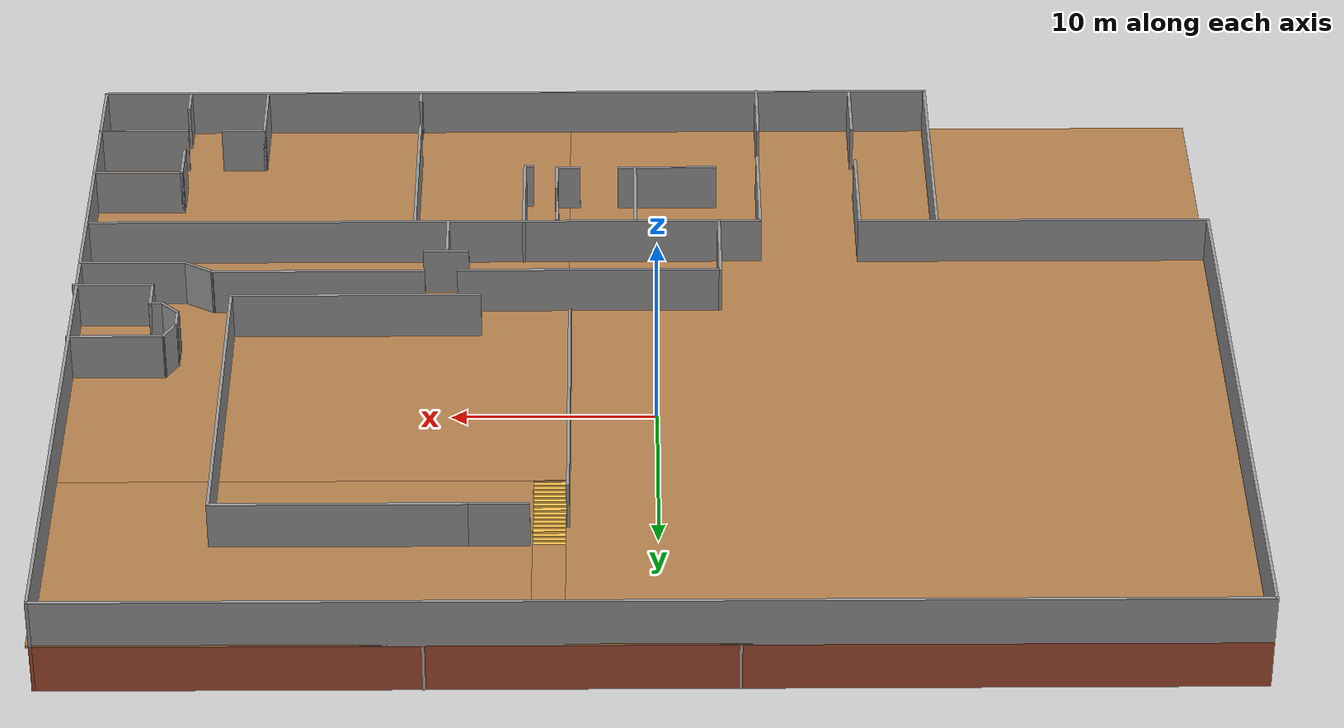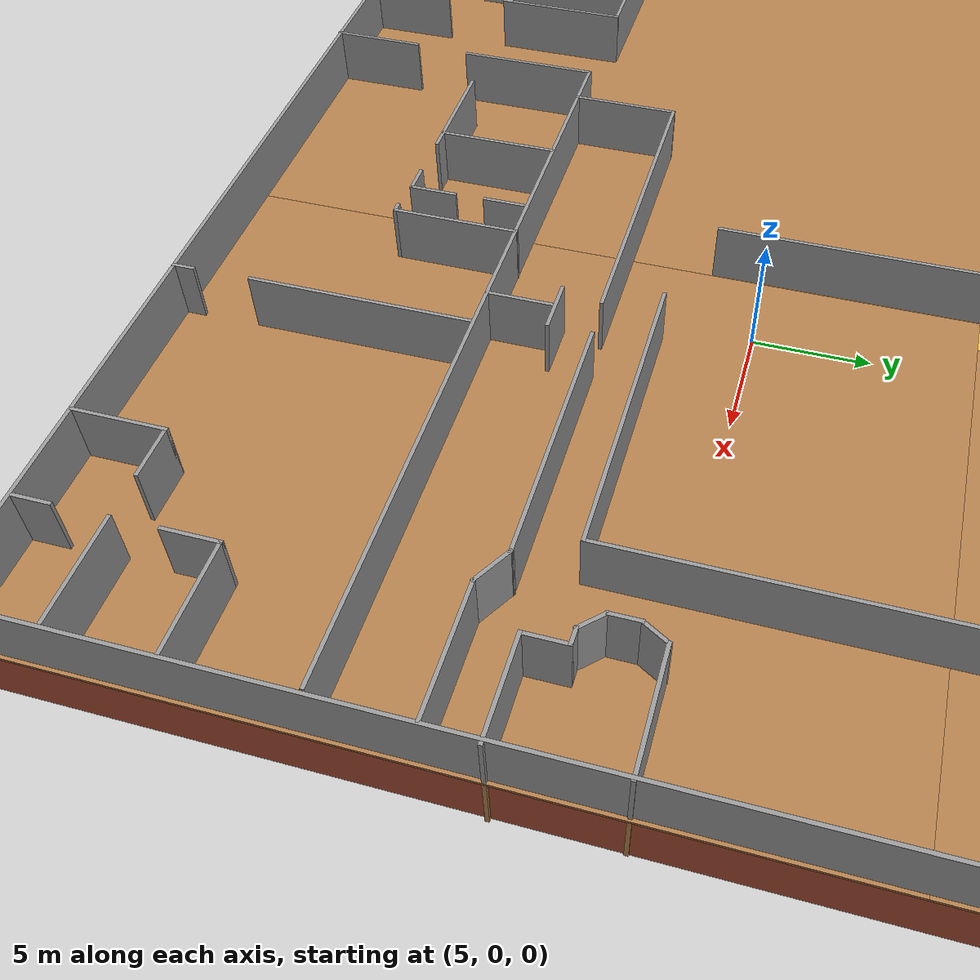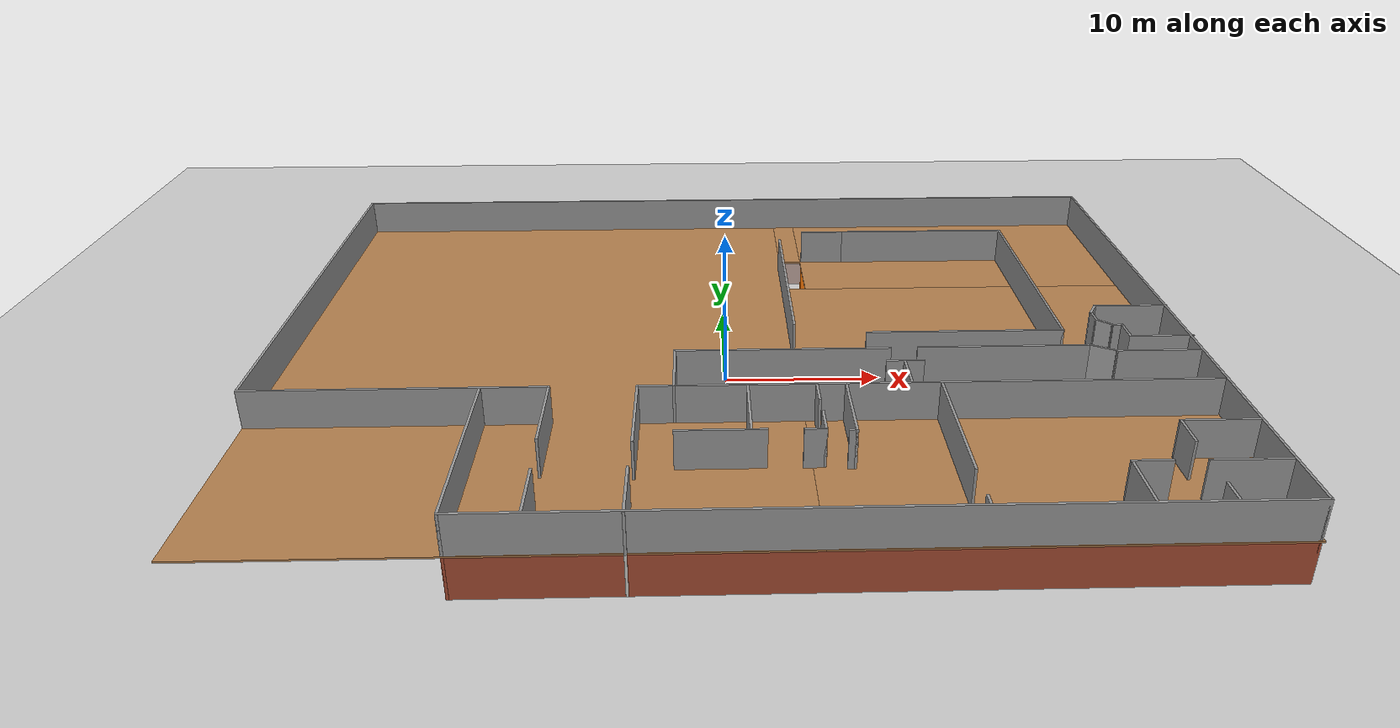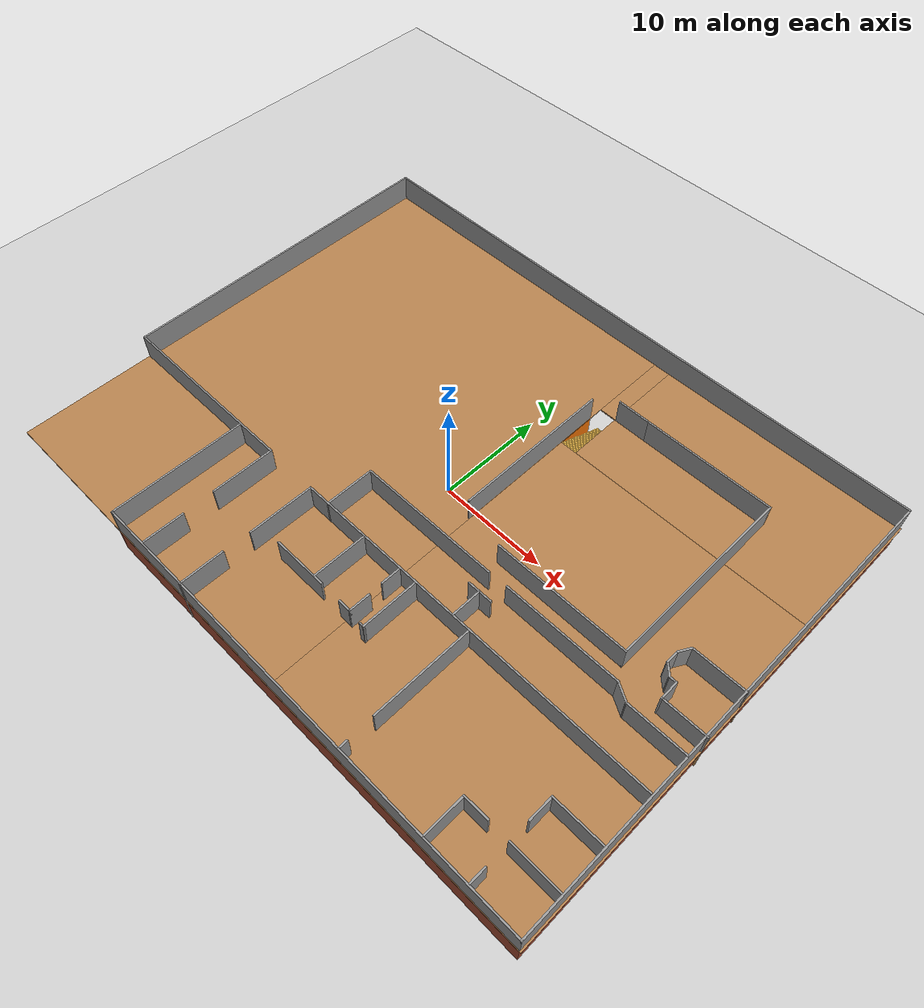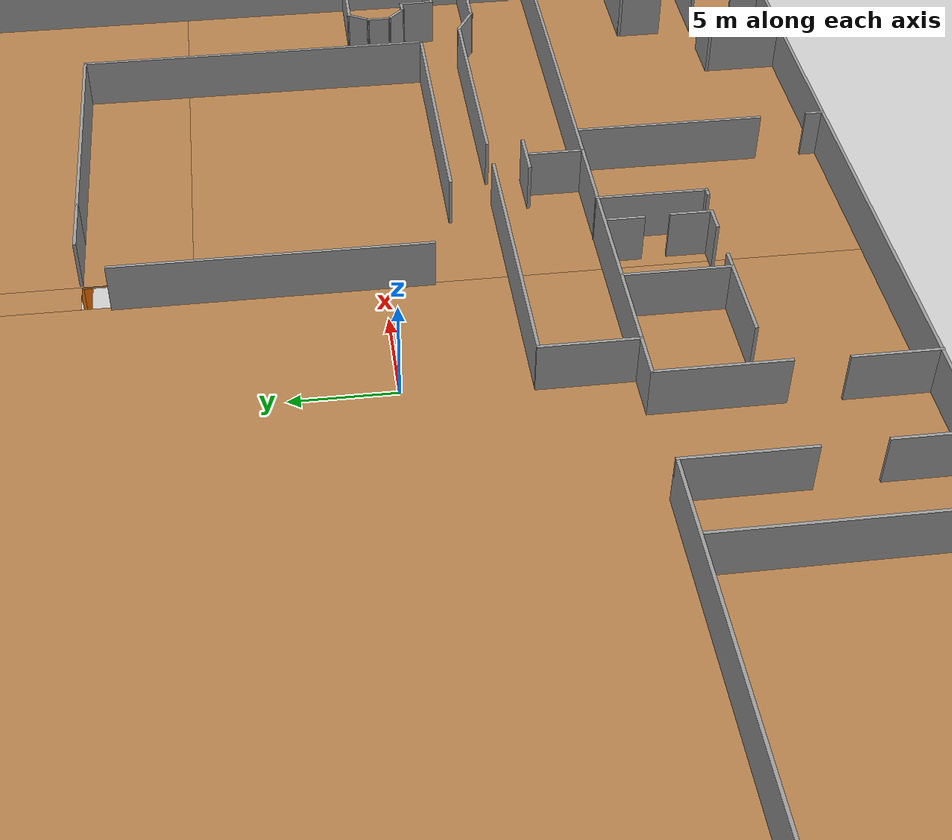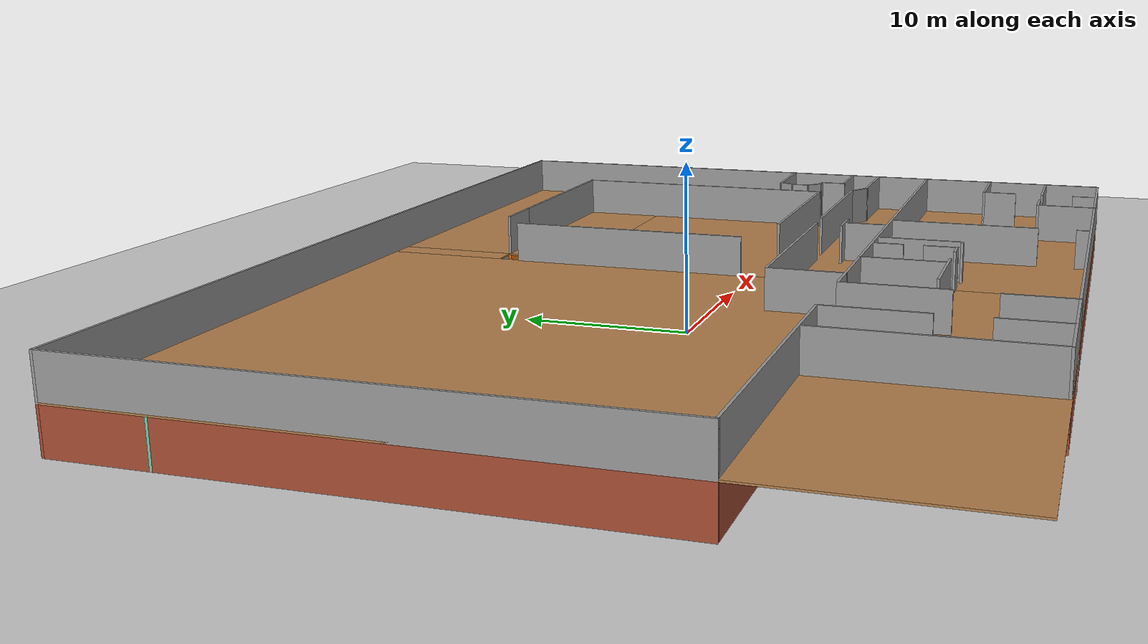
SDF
<sdf version="1.7">
 <world name="default">
  <light name="sun" type="directional">
   <pose>0 0 10 0 -0 0</pose>
   <diffuse>0.8 0.8 0.8 1</diffuse>
   <specular>0.2 0.2 0.2 1</specular>
   <attenuation>
    <range>1000</range>
    <constant>0.9</constant>
    <linear>0.01</linear>
    <quadratic>0.001</quadratic>
   </attenuation>
   <direction>-0.5 0.1 -0.9</direction>
   <spot><inner_angle>0</inner_angle><outer_angle>0</outer_angle><falloff>0</falloff></spot>
  </light>
  <model name="ground_plane">
   <static>1</static>
   <link name="link">
    <collision name="collision">
     <geometry><plane><normal>0 0 1</normal><size>100 100</size></plane></geometry>
     <surface><friction><ode><mu>100</mu><mu2>50</mu2></ode></friction></surface>
    </collision>
    <visual name="visual">
     <cast_shadows>0</cast_shadows>
     <geometry><plane><normal>0 0 1</normal><size>100 100</size></plane></geometry>
     <material>
      <script><uri>file://media/materials/scripts/gazebo.material</uri><name>Gazebo/Grey</name></script>
     </material>
    </visual>
   </link>
  </model>
  <gravity>0 0 -9.8</gravity>
  <magnetic_field>6e-06 2.3e-05 -4.2e-05</magnetic_field>
  <atmosphere type="adiabatic"/>
  <physics type="ode">
   <max_step_size>0.001</max_step_size>
   <real_time_factor>1</real_time_factor>
   <real_time_update_rate>1000</real_time_update_rate>
  </physics>
  <scene><ambient>0.4 0.4 0.4 1</ambient><background>0.7 0.7 0.7 1</background><shadows>1</shadows></scene>
  <spherical_coordinates>
   <surface_model>EARTH_WGS84</surface_model>
   <latitude_deg>48.354717</latitude_deg>
   <longitude_deg>15.884882</longitude_deg>
   <elevation>0</elevation>
   <heading_deg>0</heading_deg>
  </spherical_coordinates>
  <model name="AKW_0">
   <pose>0.482897 -0.466564 0 0 -0 0</pose>
   <link name="Floor_1">
    <pose>0.000791 -0.015384 2.5 0 -0 0</pose>
    <visual name="Floor_1_Visual_0">
     <pose>-12.1136 0 0.05 0 -0 0</pose>
     <geometry><box><size>31.911 43.2858 0.1</size></box></geometry>
     <material>
      <script><uri>file://media/materials/scripts/gazebo.material</uri><name>Gazebo/Wood</name></script>
      <ambient>0.435294 0.796078 0.67451 1</ambient>
     </material>
     <meta><layer>1</layer></meta>
    </visual>
    <collision name="Floor_1_Collision_0">
     <geometry><box><size>31.911 43.2858 0.1</size></box></geometry>
     <pose>-12.1136 0 0.05 0 -0 0</pose>
    </collision>
    <visual name="Floor_1_Visual_1">
     <pose>15.9555 -6.20457 0.05 0 -0 0</pose>
     <geometry><box><size>24.2273 30.8766 0.1</size></box></geometry>
     <material>
      <script><uri>file://media/materials/scripts/gazebo.material</uri><name>Gazebo/Wood</name></script>
      <ambient>0.435294 0.796078 0.67451 1</ambient>
     </material>
     <meta><layer>1</layer></meta>
    </visual>
    <collision name="Floor_1_Collision_1">
     <geometry><box><size>24.2273 30.8766 0.1</size></box></geometry>
     <pose>15.9555 -6.20457 0.05 0 -0 0</pose>
    </collision>
    <visual name="Floor_1_Visual_2">
     <pose>16.734 15.4383 0.05 0 -0 0</pose>
     <geometry><box><size>22.6703 12.4091 0.1</size></box></geometry>
     <material>
      <script><uri>file://media/materials/scripts/gazebo.material</uri><name>Gazebo/Wood</name></script>
      <ambient>0.435294 0.796078 0.67451 1</ambient>
     </material>
     <meta><layer>1</layer></meta>
    </visual>
    <collision name="Floor_1_Collision_2">
     <geometry><box><size>22.6703 12.4091 0.1</size></box></geometry>
     <pose>16.734 15.4383 0.05 0 -0 0</pose>
    </collision>
    <visual name="Floor_1_Visual_3">
     <pose>4.62037 17.9383 0.05 0 -0 0</pose>
     <geometry><box><size>1.557 7.40913 0.1</size></box></geometry>
     <material>
      <script><uri>file://media/materials/scripts/gazebo.material</uri><name>Gazebo/Wood</name></script>
      <ambient>0.435294 0.796078 0.67451 1</ambient>
     </material>
     <meta><layer>1</layer></meta>
    </visual>
    <collision name="Floor_1_Collision_3">
     <geometry><box><size>1.557 7.40913 0.1</size></box></geometry>
     <pose>4.62037 17.9383 0.05 0 -0 0</pose>
    </collision>
   </link>
   <link name="Stairs_1">
    <visual name="Stairs_1_Visual_0">
     <pose>4.62116 14.1184 0.05 0 -0 0</pose>
     <geometry><box><size>1.557 0.2 0.1</size></box></geometry>
     <material>
      <script><uri>file://media/materials/scripts/gazebo.material</uri><name>Gazebo/Grey</name></script>
      <ambient>1 0.764706 0.305882 1</ambient>
     </material>
     <meta><layer>0</layer></meta>
    </visual>
    <collision name="Stairs_1_Collision_0">
     <geometry><box><size>1.557 0.2 0.1</size></box></geometry>
     <pose>4.62116 14.1184 0.05 0 -0 0</pose>
    </collision>
    <visual name="Stairs_1_Visual_1">
     <pose>4.62116 13.9184 0.15 0 -0 0</pose>
     <geometry><box><size>1.557 0.2 0.1</size></box></geometry>
     <material>
      <script><uri>file://media/materials/scripts/gazebo.material</uri><name>Gazebo/Grey</name></script>
      <ambient>1 0.764706 0.305882 1</ambient>
     </material>
     <meta><layer>0</layer></meta>
    </visual>
    <collision name="Stairs_1_Collision_1">
     <geometry><box><size>1.557 0.2 0.1</size></box></geometry>
     <pose>4.62116 13.9184 0.15 0 -0 0</pose>
    </collision>
    <visual name="Stairs_1_Visual_2">
     <pose>4.62116 13.7184 0.25 0 -0 0</pose>
     <geometry><box><size>1.557 0.2 0.1</size></box></geometry>
     <material>
      <script><uri>file://media/materials/scripts/gazebo.material</uri><name>Gazebo/Grey</name></script>
      <ambient>1 0.764706 0.305882 1</ambient>
     </material>
     <meta><layer>0</layer></meta>
    </visual>
    <collision name="Stairs_1_Collision_2">
     <geometry><box><size>1.557 0.2 0.1</size></box></geometry>
     <pose>4.62116 13.7184 0.25 0 -0 0</pose>
    </collision>
    <visual name="Stairs_1_Visual_3">
     <pose>4.62116 13.5184 0.35 0 -0 0</pose>
     <geometry><box><size>1.557 0.2 0.1</size></box></geometry>
     <material>
      <script><uri>file://media/materials/scripts/gazebo.material</uri><name>Gazebo/Grey</name></script>
      <ambient>1 0.764706 0.305882 1</ambient>
     </material>
     <meta><layer>0</layer></meta>
    </visual>
    <collision name="Stairs_1_Collision_3">
     <geometry><box><size>1.557 0.2 0.1</size></box></geometry>
     <pose>4.62116 13.5184 0.35 0 -0 0</pose>
    </collision>
    <visual name="Stairs_1_Visual_4">
     <pose>4.62116 13.3184 0.45 0 -0 0</pose>
     <geometry><box><size>1.557 0.2 0.1</size></box></geometry>
     <material>
      <script><uri>file://media/materials/scripts/gazebo.material</uri><name>Gazebo/Grey</name></script>
      <ambient>1 0.764706 0.305882 1</ambient>
     </material>
     <meta><layer>0</layer></meta>
    </visual>
    <collision name="Stairs_1_Collision_4">
     <geometry><box><size>1.557 0.2 0.1</size></box></geometry>
     <pose>4.62116 13.3184 0.45 0 -0 0</pose>
    </collision>
    <visual name="Stairs_1_Visual_5">
     <pose>4.62116 13.1184 0.55 0 -0 0</pose>
     <geometry><box><size>1.557 0.2 0.1</size></box></geometry>
     <material>
      <script><uri>file://media/materials/scripts/gazebo.material</uri><name>Gazebo/Grey</name></script>
      <ambient>1 0.764706 0.305882 1</ambient>
     </material>
     <meta><layer>0</layer></meta>
    </visual>
    <collision name="Stairs_1_Collision_5">
     <geometry><box><size>1.557 0.2 0.1</size></box></geometry>
     <pose>4.62116 13.1184 0.55 0 -0 0</pose>
    </collision>
    <visual name="Stairs_1_Visual_6">
     <pose>4.62116 12.9184 0.65 0 -0 0</pose>
     <geometry><box><size>1.557 0.2 0.1</size></box></geometry>
     <material>
      <script><uri>file://media/materials/scripts/gazebo.material</uri><name>Gazebo/Grey</name></script>
      <ambient>1 0.764706 0.305882 1</ambient>
     </material>
     <meta><layer>0</layer></meta>
    </visual>
    <collision name="Stairs_1_Collision_6">
     <geometry><box><size>1.557 0.2 0.1</size></box></geometry>
     <pose>4.62116 12.9184 0.65 0 -0 0</pose>
    </collision>
    <visual name="Stairs_1_Visual_7">
     <pose>4.62116 12.7184 0.75 0 -0 0</pose>
     <geometry><box><size>1.557 0.2 0.1</size></box></geometry>
     <material>
      <script><uri>file://media/materials/scripts/gazebo.material</uri><name>Gazebo/Grey</name></script>
      <ambient>1 0.764706 0.305882 1</ambient>
     </material>
     <meta><layer>0</layer></meta>
    </visual>
    <collision name="Stairs_1_Collision_7">
     <geometry><box><size>1.557 0.2 0.1</size></box></geometry>
     <pose>4.62116 12.7184 0.75 0 -0 0</pose>
    </collision>
    <visual name="Stairs_1_Visual_8">
     <pose>4.62116 12.5184 0.85 0 -0 0</pose>
     <geometry><box><size>1.557 0.2 0.1</size></box></geometry>
     <material>
      <script><uri>file://media/materials/scripts/gazebo.material</uri><name>Gazebo/Grey</name></script>
      <ambient>1 0.764706 0.305882 1</ambient>
     </material>
     <meta><layer>0</layer></meta>
    </visual>
    <collision name="Stairs_1_Collision_8">
     <geometry><box><size>1.557 0.2 0.1</size></box></geometry>
     <pose>4.62116 12.5184 0.85 0 -0 0</pose>
    </collision>
    <visual name="Stairs_1_Visual_9">
     <pose>4.62116 12.3184 0.95 0 -0 0</pose>
     <geometry><box><size>1.557 0.2 0.1</size></box></geometry>
     <material>
      <script><uri>file://media/materials/scripts/gazebo.material</uri><name>Gazebo/Grey</name></script>
      <ambient>1 0.764706 0.305882 1</ambient>
     </material>
     <meta><layer>0</layer></meta>
    </visual>
    <collision name="Stairs_1_Collision_9">
     <geometry><box><size>1.557 0.2 0.1</size></box></geometry>
     <pose>4.62116 12.3184 0.95 0 -0 0</pose>
    </collision>
    <visual name="Stairs_1_Visual_10">
     <pose>4.62116 12.1184 1.05 0 -0 0</pose>
     <geometry><box><size>1.557 0.2 0.1</size></box></geometry>
     <material>
      <script><uri>file://media/materials/scripts/gazebo.material</uri><name>Gazebo/Grey</name></script>
      <ambient>1 0.764706 0.305882 1</ambient>
     </material>
     <meta><layer>0</layer></meta>
    </visual>
    <collision name="Stairs_1_Collision_10">
     <geometry><box><size>1.557 0.2 0.1</size></box></geometry>
     <pose>4.62116 12.1184 1.05 0 -0 0</pose>
    </collision>
    <visual name="Stairs_1_Visual_11">
     <pose>4.62116 11.9184 1.15 0 -0 0</pose>
     <geometry><box><size>1.557 0.2 0.1</size></box></geometry>
     <material>
      <script><uri>file://media/materials/scripts/gazebo.material</uri><name>Gazebo/Grey</name></script>
      <ambient>1 0.764706 0.305882 1</ambient>
     </material>
     <meta><layer>0</layer></meta>
    </visual>
    <collision name="Stairs_1_Collision_11">
     <geometry><box><size>1.557 0.2 0.1</size></box></geometry>
     <pose>4.62116 11.9184 1.15 0 -0 0</pose>
    </collision>
    <visual name="Stairs_1_Visual_12">
     <pose>4.62116 11.7184 1.25 0 -0 0</pose>
     <geometry><box><size>1.557 0.2 0.1</size></box></geometry>
     <material>
      <script><uri>file://media/materials/scripts/gazebo.material</uri><name>Gazebo/Grey</name></script>
      <ambient>1 0.764706 0.305882 1</ambient>
     </material>
     <meta><layer>0</layer></meta>
    </visual>
    <collision name="Stairs_1_Collision_12">
     <geometry><box><size>1.557 0.2 0.1</size></box></geometry>
     <pose>4.62116 11.7184 1.25 0 -0 0</pose>
    </collision>
    <visual name="Stairs_1_Visual_13">
     <pose>4.62116 11.5184 1.35 0 -0 0</pose>
     <geometry><box><size>1.557 0.2 0.1</size></box></geometry>
     <material>
      <script><uri>file://media/materials/scripts/gazebo.material</uri><name>Gazebo/Grey</name></script>
      <ambient>1 0.764706 0.305882 1</ambient>
     </material>
     <meta><layer>0</layer></meta>
    </visual>
    <collision name="Stairs_1_Collision_13">
     <geometry><box><size>1.557 0.2 0.1</size></box></geometry>
     <pose>4.62116 11.5184 1.35 0 -0 0</pose>
    </collision>
    <visual name="Stairs_1_Visual_14">
     <pose>4.62116 11.3184 1.45 0 -0 0</pose>
     <geometry><box><size>1.557 0.2 0.1</size></box></geometry>
     <material>
      <script><uri>file://media/materials/scripts/gazebo.material</uri><name>Gazebo/Grey</name></script>
      <ambient>1 0.764706 0.305882 1</ambient>
     </material>
     <meta><layer>0</layer></meta>
    </visual>
    <collision name="Stairs_1_Collision_14">
     <geometry><box><size>1.557 0.2 0.1</size></box></geometry>
     <pose>4.62116 11.3184 1.45 0 -0 0</pose>
    </collision>
    <visual name="Stairs_1_Visual_15">
     <pose>4.62116 11.1184 1.55 0 -0 0</pose>
     <geometry><box><size>1.557 0.2 0.1</size></box></geometry>
     <material>
      <script><uri>file://media/materials/scripts/gazebo.material</uri><name>Gazebo/Grey</name></script>
      <ambient>1 0.764706 0.305882 1</ambient>
     </material>
     <meta><layer>0</layer></meta>
    </visual>
    <collision name="Stairs_1_Collision_15">
     <geometry><box><size>1.557 0.2 0.1</size></box></geometry>
     <pose>4.62116 11.1184 1.55 0 -0 0</pose>
    </collision>
    <visual name="Stairs_1_Visual_16">
     <pose>4.62116 10.9184 1.65 0 -0 0</pose>
     <geometry><box><size>1.557 0.2 0.1</size></box></geometry>
     <material>
      <script><uri>file://media/materials/scripts/gazebo.material</uri><name>Gazebo/Grey</name></script>
      <ambient>1 0.764706 0.305882 1</ambient>
     </material>
     <meta><layer>0</layer></meta>
    </visual>
    <collision name="Stairs_1_Collision_16">
     <geometry><box><size>1.557 0.2 0.1</size></box></geometry>
     <pose>4.62116 10.9184 1.65 0 -0 0</pose>
    </collision>
    <visual name="Stairs_1_Visual_17">
     <pose>4.62116 10.7184 1.75 0 -0 0</pose>
     <geometry><box><size>1.557 0.2 0.1</size></box></geometry>
     <material>
      <script><uri>file://media/materials/scripts/gazebo.material</uri><name>Gazebo/Grey</name></script>
      <ambient>1 0.764706 0.305882 1</ambient>
     </material>
     <meta><layer>0</layer></meta>
    </visual>
    <collision name="Stairs_1_Collision_17">
     <geometry><box><size>1.557 0.2 0.1</size></box></geometry>
     <pose>4.62116 10.7184 1.75 0 -0 0</pose>
    </collision>
    <visual name="Stairs_1_Visual_18">
     <pose>4.62116 10.5184 1.85 0 -0 0</pose>
     <geometry><box><size>1.557 0.2 0.1</size></box></geometry>
     <material>
      <script><uri>file://media/materials/scripts/gazebo.material</uri><name>Gazebo/Grey</name></script>
      <ambient>1 0.764706 0.305882 1</ambient>
     </material>
     <meta><layer>0</layer></meta>
    </visual>
    <collision name="Stairs_1_Collision_18">
     <geometry><box><size>1.557 0.2 0.1</size></box></geometry>
     <pose>4.62116 10.5184 1.85 0 -0 0</pose>
    </collision>
    <visual name="Stairs_1_Visual_19">
     <pose>4.62116 10.3184 1.95 0 -0 0</pose>
     <geometry><box><size>1.557 0.2 0.1</size></box></geometry>
     <material>
      <script><uri>file://media/materials/scripts/gazebo.material</uri><name>Gazebo/Grey</name></script>
      <ambient>1 0.764706 0.305882 1</ambient>
     </material>
     <meta><layer>0</layer></meta>
    </visual>
    <collision name="Stairs_1_Collision_19">
     <geometry><box><size>1.557 0.2 0.1</size></box></geometry>
     <pose>4.62116 10.3184 1.95 0 -0 0</pose>
    </collision>
    <visual name="Stairs_1_Visual_20">
     <pose>4.62116 10.1184 2.05 0 -0 0</pose>
     <geometry><box><size>1.557 0.2 0.1</size></box></geometry>
     <material>
      <script><uri>file://media/materials/scripts/gazebo.material</uri><name>Gazebo/Grey</name></script>
      <ambient>1 0.764706 0.305882 1</ambient>
     </material>
     <meta><layer>0</layer></meta>
    </visual>
    <collision name="Stairs_1_Collision_20">
     <geometry><box><size>1.557 0.2 0.1</size></box></geometry>
     <pose>4.62116 10.1184 2.05 0 -0 0</pose>
    </collision>
    <visual name="Stairs_1_Visual_21">
     <pose>4.62116 9.91837 2.15 0 -0 0</pose>
     <geometry><box><size>1.557 0.2 0.1</size></box></geometry>
     <material>
      <script><uri>file://media/materials/scripts/gazebo.material</uri><name>Gazebo/Grey</name></script>
      <ambient>1 0.764706 0.305882 1</ambient>
     </material>
     <meta><layer>0</layer></meta>
    </visual>
    <collision name="Stairs_1_Collision_21">
     <geometry><box><size>1.557 0.2 0.1</size></box></geometry>
     <pose>4.62116 9.91837 2.15 0 -0 0</pose>
    </collision>
    <visual name="Stairs_1_Visual_22">
     <pose>4.62116 9.71837 2.25 0 -0 0</pose>
     <geometry><box><size>1.557 0.2 0.1</size></box></geometry>
     <material>
      <script><uri>file://media/materials/scripts/gazebo.material</uri><name>Gazebo/Grey</name></script>
      <ambient>1 0.764706 0.305882 1</ambient>
     </material>
     <meta><layer>0</layer></meta>
    </visual>
    <collision name="Stairs_1_Collision_22">
     <geometry><box><size>1.557 0.2 0.1</size></box></geometry>
     <pose>4.62116 9.71837 2.25 0 -0 0</pose>
    </collision>
    <visual name="Stairs_1_Visual_23">
     <pose>4.62116 9.51837 2.35 0 -0 0</pose>
     <geometry><box><size>1.557 0.2 0.1</size></box></geometry>
     <material>
      <script><uri>file://media/materials/scripts/gazebo.material</uri><name>Gazebo/Grey</name></script>
      <ambient>1 0.764706 0.305882 1</ambient>
     </material>
     <meta><layer>0</layer></meta>
    </visual>
    <collision name="Stairs_1_Collision_23">
     <geometry><box><size>1.557 0.2 0.1</size></box></geometry>
     <pose>4.62116 9.51837 2.35 0 -0 0</pose>
    </collision>
    <visual name="Stairs_1_Visual_24">
     <pose>4.62116 9.31837 2.45 0 -0 0</pose>
     <geometry><box><size>1.557 0.2 0.1</size></box></geometry>
     <material>
      <script><uri>file://media/materials/scripts/gazebo.material</uri><name>Gazebo/Grey</name></script>
      <ambient>1 0.764706 0.305882 1</ambient>
     </material>
     <meta><layer>0</layer></meta>
    </visual>
    <collision name="Stairs_1_Collision_24">
     <geometry><box><size>1.557 0.2 0.1</size></box></geometry>
     <pose>4.62116 9.31837 2.45 0 -0 0</pose>
    </collision>
   </link>
   <link name="Wall_0">
    <collision name="Wall_0_Collision">
     <geometry><box><size>42.5 0.15 2.5</size></box></geometry>
     <pose>0 0 1.25 0 -0 0</pose>
    </collision>
    <visual name="Wall_0_Visual">
     <pose>0 0 1.25 0 -0 0</pose>
     <geometry><box><size>42.5 0.15 2.5</size></box></geometry>
     <material>
      <script><uri>file://media/materials/scripts/gazebo.material</uri><name>Gazebo/Bricks</name></script>
      <ambient>1 1 1 1</ambient>
     </material>
     <meta><layer>0</layer></meta>
    </visual>
    <pose>6.68165 -21.5475 0 0 -0 0</pose>
   </link>
   <link name="Wall_1">
    <collision name="Wall_1_Collision">
     <geometry><box><size>43.25 0.15 2.5</size></box></geometry>
     <pose>0 0 1.25 0 -0 0</pose>
    </collision>
    <visual name="Wall_1_Visual">
     <pose>0 0 1.25 0 -0 0</pose>
     <geometry><box><size>43.25 0.15 2.5</size></box></geometry>
     <material>
      <script><uri>file://media/materials/scripts/gazebo.material</uri><name>Gazebo/Bricks</name></script>
      <ambient>1 1 1 1</ambient>
     </material>
     <meta><layer>0</layer></meta>
    </visual>
    <pose>27.8567 0.002503 0 0 -0 1.5708</pose>
   </link>
   <link name="Wall_10">
    <collision name="Wall_10_Collision">
     <geometry><box><size>33.5 0.15 2.5</size></box></geometry>
     <pose>0 0 1.25 0 -0 0</pose>
    </collision>
    <visual name="Wall_10_Visual">
     <pose>0 0 1.25 0 -0 0</pose>
     <geometry><box><size>33.5 0.15 2.5</size></box></geometry>
     <material>
      <script><uri>file://media/materials/scripts/gazebo.material</uri><name>Gazebo/CeilingTiled</name></script>
      <ambient>1 1 1 1</ambient>
     </material>
     <meta><layer>0</layer></meta>
    </visual>
    <pose>10.9914 -9.37368 0 0 -0 0</pose>
   </link>
   <link name="Wall_100">
    <collision name="Wall_100_Collision">
     <geometry><box><size>4.75 0.15 2.5</size></box></geometry>
     <pose>0 0 1.25 0 -0 0</pose>
    </collision>
    <visual name="Wall_100_Visual">
     <pose>0 0 1.25 0 -0 0</pose>
     <geometry><box><size>4.75 0.15 2.5</size></box></geometry>
     <material>
      <script><uri>file://media/materials/scripts/gazebo.material</uri><name>Gazebo/Wood</name></script>
      <ambient>1 1 1 1</ambient>
     </material>
     <meta><layer>0</layer></meta>
    </visual>
    <pose>25.6171 0.610399 0 0 -0 3.14159</pose>
   </link>
   <link name="Wall_101">
    <collision name="Wall_101_Collision">
     <geometry><box><size>1.25 0.15 2.5</size></box></geometry>
     <pose>0 0 1.25 0 -0 0</pose>
    </collision>
    <visual name="Wall_101_Visual">
     <pose>0 0 1.25 0 -0 0</pose>
     <geometry><box><size>1.25 0.15 2.5</size></box></geometry>
     <material>
      <script><uri>file://media/materials/scripts/gazebo.material</uri><name>Gazebo/Wood</name></script>
      <ambient>1 1 1 1</ambient>
     </material>
     <meta><layer>0</layer></meta>
    </visual>
    <pose>23.0421 0.134085 0 0 -0 -2.0944</pose>
   </link>
   <link name="Wall_102">
    <collision name="Wall_102_Collision">
     <geometry><box><size>1.25 0.15 2.5</size></box></geometry>
     <pose>0 0 1.25 0 -0 0</pose>
    </collision>
    <visual name="Wall_102_Visual">
     <pose>0 0 1.25 0 -0 0</pose>
     <geometry><box><size>1.25 0.15 2.5</size></box></geometry>
     <material>
      <script><uri>file://media/materials/scripts/gazebo.material</uri><name>Gazebo/Wood</name></script>
      <ambient>1 1 1 1</ambient>
     </material>
     <meta><layer>0</layer></meta>
    </visual>
    <pose>22.7671 -0.892229 0 0 -0 -1.5708</pose>
   </link>
   <link name="Wall_103">
    <collision name="Wall_103_Collision">
     <geometry><box><size>1.25 0.15 2.5</size></box></geometry>
     <pose>0 0 1.25 0 -0 0</pose>
    </collision>
    <visual name="Wall_103_Visual">
     <pose>0 0 1.25 0 -0 0</pose>
     <geometry><box><size>1.25 0.15 2.5</size></box></geometry>
     <material>
      <script><uri>file://media/materials/scripts/gazebo.material</uri><name>Gazebo/Wood</name></script>
      <ambient>1 1 1 1</ambient>
     </material>
     <meta><layer>0</layer></meta>
    </visual>
    <pose>23.156 -1.83114 0 0 -0 -0.785398</pose>
   </link>
   <link name="Wall_104">
    <collision name="Wall_104_Collision">
     <geometry><box><size>0.75 0.15 2.5</size></box></geometry>
     <pose>0 0 1.25 0 -0 0</pose>
    </collision>
    <visual name="Wall_104_Visual">
     <pose>0 0 1.25 0 -0 0</pose>
     <geometry><box><size>0.75 0.15 2.5</size></box></geometry>
     <material>
      <script><uri>file://media/materials/scripts/gazebo.material</uri><name>Gazebo/Wood</name></script>
      <ambient>1 1 1 1</ambient>
     </material>
     <meta><layer>0</layer></meta>
    </visual>
    <pose>23.8449 -2.22005 0 0 -0 0</pose>
   </link>
   <link name="Wall_105">
    <collision name="Wall_105_Collision">
     <geometry><box><size>1.75 0.15 2.5</size></box></geometry>
     <pose>0 0 1.25 0 -0 0</pose>
    </collision>
    <visual name="Wall_105_Visual">
     <pose>0 0 1.25 0 -0 0</pose>
     <geometry><box><size>1.75 0.15 2.5</size></box></geometry>
     <material>
      <script><uri>file://media/materials/scripts/gazebo.material</uri><name>Gazebo/Wood</name></script>
      <ambient>1 1 1 1</ambient>
     </material>
     <meta><layer>0</layer></meta>
    </visual>
    <pose>24.1449 -3.02005 0 0 -0 -1.5708</pose>
   </link>
   <link name="Wall_106">
    <collision name="Wall_106_Collision">
     <geometry><box><size>4 0.15 2.5</size></box></geometry>
     <pose>0 0 1.25 0 -0 0</pose>
    </collision>
    <visual name="Wall_106_Visual">
     <pose>0 0 1.25 0 -0 0</pose>
     <geometry><box><size>4 0.15 2.5</size></box></geometry>
     <material>
      <script><uri>file://media/materials/scripts/gazebo.material</uri><name>Gazebo/Wood</name></script>
      <ambient>1 1 1 1</ambient>
     </material>
     <meta><layer>0</layer></meta>
    </visual>
    <pose>26.0699 -3.82005 0 0 -0 0</pose>
   </link>
   <link name="Wall_108">
    <collision name="Wall_108_Collision">
     <geometry><box><size>5 0.15 2.5</size></box></geometry>
     <pose>0 0 1.25 0 -0 0</pose>
    </collision>
    <visual name="Wall_108_Visual">
     <pose>0 0 1.25 0 -0 0</pose>
     <geometry><box><size>5 0.15 2.5</size></box></geometry>
     <material>
      <script><uri>file://media/materials/scripts/gazebo.material</uri><name>Gazebo/Grey</name></script>
      <ambient>0.996078 0.47451 0.0196078 1</ambient>
     </material>
     <meta><layer>0</layer></meta>
    </visual>
    <pose>-1.29696 12.7755 0 0 -0 3.14159</pose>
   </link>
   <link name="Wall_109">
    <collision name="Wall_109_Collision">
     <geometry><box><size>7 0.15 2.5</size></box></geometry>
     <pose>0 0 1.25 0 -0 0</pose>
    </collision>
    <visual name="Wall_109_Visual">
     <pose>0 0 1.25 0 -0 0</pose>
     <geometry><box><size>7 0.15 2.5</size></box></geometry>
     <material>
      <script><uri>file://media/materials/scripts/gazebo.material</uri><name>Gazebo/Grey</name></script>
      <ambient>0.996078 0.47451 0.0196078 1</ambient>
     </material>
     <meta><layer>0</layer></meta>
    </visual>
    <pose>-3.72196 9.35053 0 0 -0 -1.5708</pose>
   </link>
   <link name="Wall_110">
    <collision name="Wall_110_Collision">
     <geometry><box><size>2 0.15 2.5</size></box></geometry>
     <pose>0 0 1.25 0 -0 0</pose>
    </collision>
    <visual name="Wall_110_Visual">
     <pose>0 0 1.25 0 -0 0</pose>
     <geometry><box><size>2 0.15 2.5</size></box></geometry>
     <material>
      <script><uri>file://media/materials/scripts/gazebo.material</uri><name>Gazebo/Grey</name></script>
      <ambient>0.996078 0.47451 0.0196078 1</ambient>
     </material>
     <meta><layer>0</layer></meta>
    </visual>
    <pose>-4.64696 5.92553 0 0 -0 3.14159</pose>
   </link>
   <link name="Wall_111">
    <collision name="Wall_111_Collision">
     <geometry><box><size>5 0.15 2.5</size></box></geometry>
     <pose>0 0 1.25 0 -0 0</pose>
    </collision>
    <visual name="Wall_111_Visual">
     <pose>0 0 1.25 0 -0 0</pose>
     <geometry><box><size>5 0.15 2.5</size></box></geometry>
     <material>
      <script><uri>file://media/materials/scripts/gazebo.material</uri><name>Gazebo/Grey</name></script>
      <ambient>0.996078 0.47451 0.0196078 1</ambient>
     </material>
     <meta><layer>0</layer></meta>
    </visual>
    <pose>-5.57196 8.35053 0 0 -0 1.5708</pose>
   </link>
   <link name="Wall_112">
    <collision name="Wall_112_Collision">
     <geometry><box><size>2 0.15 2.5</size></box></geometry>
     <pose>0 0 1.25 0 -0 0</pose>
    </collision>
    <visual name="Wall_112_Visual">
     <pose>0 0 1.25 0 -0 0</pose>
     <geometry><box><size>2 0.15 2.5</size></box></geometry>
     <material>
      <script><uri>file://media/materials/scripts/gazebo.material</uri><name>Gazebo/Grey</name></script>
      <ambient>0.996078 0.47451 0.0196078 1</ambient>
     </material>
     <meta><layer>0</layer></meta>
    </visual>
    <pose>-4.64696 10.7755 0 0 -0 0</pose>
   </link>
   <link name="Wall_114">
    <collision name="Wall_114_Collision">
     <geometry><box><size>2 0.15 2.5</size></box></geometry>
     <pose>0 0 1.25 0 -0 0</pose>
    </collision>
    <visual name="Wall_114_Visual">
     <pose>0 0 1.25 0 -0 0</pose>
     <geometry><box><size>2 0.15 2.5</size></box></geometry>
     <material>
      <script><uri>file://media/materials/scripts/gazebo.material</uri><name>Gazebo/Grey</name></script>
      <ambient>0.996078 0.47451 0.0196078 1</ambient>
     </material>
     <meta><layer>0</layer></meta>
    </visual>
    <pose>-2.79696 10.7755 0 0 -0 0</pose>
   </link>
   <link name="Wall_115">
    <collision name="Wall_115_Collision">
     <geometry><box><size>1.25 0.15 2.5</size></box></geometry>
     <pose>0 0 1.25 0 -0 0</pose>
    </collision>
    <visual name="Wall_115_Visual">
     <pose>0 0 1.25 0 -0 0</pose>
     <geometry><box><size>1.25 0.15 2.5</size></box></geometry>
     <material>
      <script><uri>file://media/materials/scripts/gazebo.material</uri><name>Gazebo/Grey</name></script>
      <ambient>0.996078 0.47451 0.0196078 1</ambient>
     </material>
     <meta><layer>0</layer></meta>
    </visual>
    <pose>-1.39565 11.0505 0 0 -0 0.523599</pose>
   </link>
   <link name="Wall_116">
    <collision name="Wall_116_Collision">
     <geometry><box><size>1.5 0.15 2.5</size></box></geometry>
     <pose>0 0 1.25 0 -0 0</pose>
    </collision>
    <visual name="Wall_116_Visual">
     <pose>0 0 1.25 0 -0 0</pose>
     <geometry><box><size>1.5 0.15 2.5</size></box></geometry>
     <material>
      <script><uri>file://media/materials/scripts/gazebo.material</uri><name>Gazebo/Grey</name></script>
      <ambient>0.996078 0.47451 0.0196078 1</ambient>
     </material>
     <meta><layer>0</layer></meta>
    </visual>
    <pose>-0.919332 12.0005 0 0 -0 1.5708</pose>
   </link>
   <link name="Wall_118">
    <collision name="Wall_118_Collision">
     <geometry><box><size>14.5 0.15 2.5</size></box></geometry>
     <pose>0 0 1.25 0 -0 0</pose>
    </collision>
    <visual name="Wall_118_Visual">
     <pose>0 0 1.25 0 -0 0</pose>
     <geometry><box><size>14.5 0.15 2.5</size></box></geometry>
     <material>
      <script><uri>file://media/materials/scripts/gazebo.material</uri><name>Gazebo/Grey</name></script>
      <ambient>0.996078 0.47451 0.0196078 1</ambient>
     </material>
     <meta><layer>0</layer></meta>
    </visual>
    <pose>3.74669 5.6278 0 0 -0 -1.5708</pose>
   </link>
   <link name="Wall_119">
    <collision name="Wall_119_Collision">
     <geometry><box><size>7.75 0.15 2.5</size></box></geometry>
     <pose>0 0 1.25 0 -0 0</pose>
    </collision>
    <visual name="Wall_119_Visual">
     <pose>0 0 1.25 0 -0 0</pose>
     <geometry><box><size>7.75 0.15 2.5</size></box></geometry>
     <material>
      <script><uri>file://media/materials/scripts/gazebo.material</uri><name>Gazebo/Grey</name></script>
      <ambient>0.996078 0.47451 0.0196078 1</ambient>
     </material>
     <meta><layer>0</layer></meta>
    </visual>
    <pose>-0.053314 -1.5472 0 0 -0 3.14159</pose>
   </link>
   <link name="Wall_12">
    <collision name="Wall_12_Collision">
     <geometry><box><size>19 0.15 2.5</size></box></geometry>
     <pose>0 0 1.25 0 -0 0</pose>
    </collision>
    <visual name="Wall_12_Visual">
     <pose>0 0 1.25 0 -0 0</pose>
     <geometry><box><size>19 0.15 2.5</size></box></geometry>
     <material>
      <script><uri>file://media/materials/scripts/gazebo.material</uri><name>Gazebo/Bricks</name></script>
      <ambient>1 1 1 1</ambient>
     </material>
     <meta><layer>0</layer></meta>
    </visual>
    <pose>-10.8959 4.66757 0 0 -0 1.5708</pose>
   </link>
   <link name="Wall_120">
    <collision name="Wall_120_Collision">
     <geometry><box><size>4.25 0.15 2.5</size></box></geometry>
     <pose>0 0 1.25 0 -0 0</pose>
    </collision>
    <visual name="Wall_120_Visual">
     <pose>0 0 1.25 0 -0 0</pose>
     <geometry><box><size>4.25 0.15 2.5</size></box></geometry>
     <material>
      <script><uri>file://media/materials/scripts/gazebo.material</uri><name>Gazebo/Grey</name></script>
      <ambient>0.996078 0.47451 0.0196078 1</ambient>
     </material>
     <meta><layer>0</layer></meta>
    </visual>
    <pose>-3.85331 0.502804 0 0 -0 1.5708</pose>
   </link>
   <link name="Wall_121">
    <collision name="Wall_121_Collision">
     <geometry><box><size>2 0.15 2.5</size></box></geometry>
     <pose>0 0 1.25 0 -0 0</pose>
    </collision>
    <visual name="Wall_121_Visual">
     <pose>0 0 1.25 0 -0 0</pose>
     <geometry><box><size>2 0.15 2.5</size></box></geometry>
     <material>
      <script><uri>file://media/materials/scripts/gazebo.material</uri><name>Gazebo/Grey</name></script>
      <ambient>0.996078 0.47451 0.0196078 1</ambient>
     </material>
     <meta><layer>0</layer></meta>
    </visual>
    <pose>-2.92831 2.5528 0 0 -0 0</pose>
   </link>
   <link name="Wall_122">
    <collision name="Wall_122_Collision">
     <geometry><box><size>0.75 0.15 2.5</size></box></geometry>
     <pose>0 0 1.25 0 -0 0</pose>
    </collision>
    <visual name="Wall_122_Visual">
     <pose>0 0 1.25 0 -0 0</pose>
     <geometry><box><size>0.75 0.15 2.5</size></box></geometry>
     <material>
      <script><uri>file://media/materials/scripts/gazebo.material</uri><name>Gazebo/Grey</name></script>
      <ambient>0.996078 0.47451 0.0196078 1</ambient>
     </material>
     <meta><layer>0</layer></meta>
    </visual>
    <pose>-1.79118 2.34067 0 0 -0 -0.785398</pose>
   </link>
   <link name="Wall_123">
    <collision name="Wall_123_Collision">
     <geometry><box><size>2 0.15 2.5</size></box></geometry>
     <pose>0 0 1.25 0 -0 0</pose>
    </collision>
    <visual name="Wall_123_Visual">
     <pose>0 0 1.25 0 -0 0</pose>
     <geometry><box><size>2 0.15 2.5</size></box></geometry>
     <material>
      <script><uri>file://media/materials/scripts/gazebo.material</uri><name>Gazebo/Grey</name></script>
      <ambient>0.996078 0.47451 0.0196078 1</ambient>
     </material>
     <meta><layer>0</layer></meta>
    </visual>
    <pose>-1.57905 1.20354 0 0 -0 -1.5708</pose>
   </link>
   <link name="Wall_124">
    <collision name="Wall_124_Collision">
     <geometry><box><size>1 0.15 2.5</size></box></geometry>
     <pose>0 0 1.25 0 -0 0</pose>
    </collision>
    <visual name="Wall_124_Visual">
     <pose>0 0 1.25 0 -0 0</pose>
     <geometry><box><size>1 0.15 2.5</size></box></geometry>
     <material>
      <script><uri>file://media/materials/scripts/gazebo.material</uri><name>Gazebo/Grey</name></script>
      <ambient>0.996078 0.47451 0.0196078 1</ambient>
     </material>
     <meta><layer>0</layer></meta>
    </visual>
    <pose>-1.15405 0.27854 0 0 -0 0</pose>
   </link>
   <link name="Wall_125">
    <collision name="Wall_125_Collision">
     <geometry><box><size>1.75 0.15 2.5</size></box></geometry>
     <pose>0 0 1.25 0 -0 0</pose>
    </collision>
    <visual name="Wall_125_Visual">
     <pose>0 0 1.25 0 -0 0</pose>
     <geometry><box><size>1.75 0.15 2.5</size></box></geometry>
     <material>
      <script><uri>file://media/materials/scripts/gazebo.material</uri><name>Gazebo/Grey</name></script>
      <ambient>0.996078 0.47451 0.0196078 1</ambient>
     </material>
     <meta><layer>0</layer></meta>
    </visual>
    <pose>-0.729049 -0.52146 0 0 -0 -1.5708</pose>
   </link>
   <link name="Wall_126">
    <collision name="Wall_126_Collision">
     <geometry><box><size>0.25 0.15 2.5</size></box></geometry>
     <pose>0 0 1.25 0 -0 0</pose>
    </collision>
    <visual name="Wall_126_Visual">
     <pose>0 0 1.25 0 -0 0</pose>
     <geometry><box><size>0.25 0.15 2.5</size></box></geometry>
     <material>
      <script><uri>file://media/materials/scripts/gazebo.material</uri><name>Gazebo/Grey</name></script>
      <ambient>0.996078 0.47451 0.0196078 1</ambient>
     </material>
     <meta><layer>0</layer></meta>
    </visual>
    <pose>-0.729049 -1.37146 0 0 -0 -1.5708</pose>
   </link>
   <link name="Wall_128">
    <collision name="Wall_128_Collision">
     <geometry><box><size>3.25 0.15 2.5</size></box></geometry>
     <pose>0 0 1.25 0 -0 0</pose>
    </collision>
    <visual name="Wall_128_Visual">
     <pose>0 0 1.25 0 -0 0</pose>
     <geometry><box><size>3.25 0.15 2.5</size></box></geometry>
     <material>
      <script><uri>file://media/materials/scripts/gazebo.material</uri><name>Gazebo/Grey</name></script>
      <ambient>0.996078 0.47451 0.0196078 1</ambient>
     </material>
     <meta><layer>0</layer></meta>
    </visual>
    <pose>5.29669 -1.5472 0 0 -0 0</pose>
   </link>
   <link name="Wall_129">
    <collision name="Wall_129_Collision">
     <geometry><box><size>2 0.15 2.5</size></box></geometry>
     <pose>0 0 1.25 0 -0 0</pose>
    </collision>
    <visual name="Wall_129_Visual">
     <pose>0 0 1.25 0 -0 0</pose>
     <geometry><box><size>2 0.15 2.5</size></box></geometry>
     <material>
      <script><uri>file://media/materials/scripts/gazebo.material</uri><name>Gazebo/Grey</name></script>
      <ambient>0.996078 0.47451 0.0196078 1</ambient>
     </material>
     <meta><layer>0</layer></meta>
    </visual>
    <pose>7.50076 -2.20127 0 0 -0 -0.785398</pose>
   </link>
   <link name="Wall_130">
    <collision name="Wall_130_Collision">
     <geometry><box><size>12.25 0.15 2.5</size></box></geometry>
     <pose>0 0 1.25 0 -0 0</pose>
    </collision>
    <visual name="Wall_130_Visual">
     <pose>0 0 1.25 0 -0 0</pose>
     <geometry><box><size>12.25 0.15 2.5</size></box></geometry>
     <material>
      <script><uri>file://media/materials/scripts/gazebo.material</uri><name>Gazebo/Grey</name></script>
      <ambient>0.996078 0.47451 0.0196078 1</ambient>
     </material>
     <meta><layer>0</layer></meta>
    </visual>
    <pose>14.2048 -2.85534 0 0 -0 0</pose>
   </link>
   <link name="Wall_131">
    <collision name="Wall_131_Collision">
     <geometry><box><size>17.25 0.15 2.5</size></box></geometry>
     <pose>0 0 1.25 0 -0 0</pose>
    </collision>
    <visual name="Wall_131_Visual">
     <pose>0 0 1.25 0 -0 0</pose>
     <geometry><box><size>17.25 0.15 2.5</size></box></geometry>
     <material>
      <script><uri>file://media/materials/scripts/gazebo.material</uri><name>Gazebo/Grey</name></script>
      <ambient>0.996078 0.47451 0.0196078 1</ambient>
     </material>
     <meta><layer>0</layer></meta>
    </visual>
    <pose>20.2548 5.69466 0 0 -0 1.5708</pose>
   </link>
   <link name="Wall_132">
    <collision name="Wall_132_Collision">
     <geometry><box><size>12 0.15 2.5</size></box></geometry>
     <pose>0 0 1.25 0 -0 0</pose>
    </collision>
    <visual name="Wall_132_Visual">
     <pose>0 0 1.25 0 -0 0</pose>
     <geometry><box><size>12 0.15 2.5</size></box></geometry>
     <material>
      <script><uri>file://media/materials/scripts/gazebo.material</uri><name>Gazebo/Grey</name></script>
      <ambient>0.996078 0.47451 0.0196078 1</ambient>
     </material>
     <meta><layer>0</layer></meta>
    </visual>
    <pose>14.3298 14.2447 0 0 -0 3.14159</pose>
   </link>
   <link name="Wall_133">
    <collision name="Wall_133_Collision">
     <geometry><box><size>3 0.15 2.5</size></box></geometry>
     <pose>0 0 1.25 0 -0 0</pose>
    </collision>
    <visual name="Wall_133_Visual">
     <pose>0 0 1.25 0 -0 0</pose>
     <geometry><box><size>3 0.15 2.5</size></box></geometry>
     <material>
      <script><uri>file://media/materials/scripts/gazebo.material</uri><name>Gazebo/Grey</name></script>
      <ambient>0.996078 0.47451 0.0196078 1</ambient>
     </material>
     <meta><layer>0</layer></meta>
    </visual>
    <pose>6.97983 14.2447 0 0 -0 3.14159</pose>
   </link>
   <link name="Wall_14">
    <collision name="Wall_14_Collision">
     <geometry><box><size>7 0.15 2.5</size></box></geometry>
     <pose>0 0 1.25 0 -0 0</pose>
    </collision>
    <visual name="Wall_14_Visual">
     <pose>0 0 1.25 0 -0 0</pose>
     <geometry><box><size>7 0.15 2.5</size></box></geometry>
     <material>
      <script><uri>file://media/materials/scripts/gazebo.material</uri><name>Gazebo/Bricks</name></script>
      <ambient>1 1 1 1</ambient>
     </material>
     <meta><layer>0</layer></meta>
    </visual>
    <pose>-14.4147 -7.24339 0 0 -0 3.14159</pose>
   </link>
   <link name="Wall_15">
    <collision name="Wall_15_Collision">
     <geometry><box><size>3.25 0.15 2.5</size></box></geometry>
     <pose>0 0 1.25 0 -0 0</pose>
    </collision>
    <visual name="Wall_15_Visual">
     <pose>0 0 1.25 0 -0 0</pose>
     <geometry><box><size>3.25 0.15 2.5</size></box></geometry>
     <material>
      <script><uri>file://media/materials/scripts/gazebo.material</uri><name>Gazebo/Bricks</name></script>
      <ambient>1 1 1 1</ambient>
     </material>
     <meta><layer>0</layer></meta>
    </visual>
    <pose>-17.8397 -5.69339 0 0 -0 1.5708</pose>
   </link>
   <link name="Wall_17">
    <collision name="Wall_17_Collision">
     <geometry><box><size>20.75 0.15 2.5</size></box></geometry>
     <pose>0 0 1.25 0 -0 0</pose>
    </collision>
    <visual name="Wall_17_Visual">
     <pose>0 0 1.25 0 -0 0</pose>
     <geometry><box><size>20.75 0.15 2.5</size></box></geometry>
     <material>
      <script><uri>file://media/materials/scripts/gazebo.material</uri><name>Gazebo/Bricks</name></script>
      <ambient>1 1 1 1</ambient>
     </material>
     <meta><layer>0</layer></meta>
    </visual>
    <pose>-17.9316 8.45068 0 0 -0 1.5708</pose>
   </link>
   <link name="Wall_18">
    <collision name="Wall_18_Collision">
     <geometry><box><size>7.13756 0.15 2.5</size></box></geometry>
     <pose>0 0 1.25 0 -0 0</pose>
    </collision>
    <visual name="Wall_18_Visual">
     <pose>0 0 1.25 0 -0 0</pose>
     <geometry><box><size>7.13756 0.15 2.5</size></box></geometry>
     <material>
      <script><uri>file://media/materials/scripts/gazebo.material</uri><name>Gazebo/Bricks</name></script>
      <ambient>1 1 1 1</ambient>
     </material>
     <meta><layer>0</layer></meta>
    </visual>
    <pose>-14.4379 18.7507 0 0 -0 0</pose>
   </link>
   <link name="Wall_19">
    <collision name="Wall_19_Collision">
     <geometry><box><size>3.2973 0.15 2.5</size></box></geometry>
     <pose>0 0 1.25 0 -0 0</pose>
    </collision>
    <visual name="Wall_19_Visual">
     <pose>0 0 1.25 0 -0 0</pose>
     <geometry><box><size>3.2973 0.15 2.5</size></box></geometry>
     <material>
      <script><uri>file://media/materials/scripts/gazebo.material</uri><name>Gazebo/Bricks</name></script>
      <ambient>1 1 1 1</ambient>
     </material>
     <meta><layer>0</layer></meta>
    </visual>
    <pose>-10.9368 17.177 0 0 -0 -1.57268</pose>
   </link>
   <link name="Wall_2">
    <collision name="Wall_2_Collision">
     <geometry><box><size>56 0.15 2.5</size></box></geometry>
     <pose>0 0 1.25 0 -0 0</pose>
    </collision>
    <visual name="Wall_2_Visual">
     <pose>0 0 1.25 0 -0 0</pose>
     <geometry><box><size>56 0.15 2.5</size></box></geometry>
     <material>
      <script><uri>file://media/materials/scripts/gazebo.material</uri><name>Gazebo/Bricks</name></script>
      <ambient>1 1 1 1</ambient>
     </material>
     <meta><layer>0</layer></meta>
    </visual>
    <pose>-0.068349 21.5525 0 0 -0 3.14159</pose>
   </link>
   <link name="Wall_21">
    <collision name="Wall_21_Collision">
     <geometry><box><size>7 0.15 2.5</size></box></geometry>
     <pose>0 0 1.25 0 -0 0</pose>
    </collision>
    <visual name="Wall_21_Visual">
     <pose>0 0 1.25 0 -0 0</pose>
     <geometry><box><size>7 0.15 2.5</size></box></geometry>
     <material>
      <script><uri>file://media/materials/scripts/gazebo.material</uri><name>Gazebo/Bricks</name></script>
      <ambient>1 1 1 1</ambient>
     </material>
     <meta><layer>0</layer></meta>
    </visual>
    <pose>-14.4748 1.61674 0 0 -0 0</pose>
   </link>
   <link name="Wall_223">
    <collision name="Wall_223_Collision">
     <geometry><box><size>42.5 0.15 2.5</size></box></geometry>
     <pose>0 0 1.25 0 -0 0</pose>
    </collision>
    <visual name="Wall_223_Visual">
     <pose>0 0 1.25 0 -0 0</pose>
     <geometry><box><size>42.5 0.15 2.5</size></box></geometry>
     <material>
      <script><uri>file://media/materials/scripts/gazebo.material</uri><name>Gazebo/Grey</name></script>
      <ambient>1 1 1 1</ambient>
     </material>
     <meta><layer>1</layer></meta>
    </visual>
    <pose>6.68165 -21.5475 2.5 0 -0 0</pose>
   </link>
   <link name="Wall_224">
    <collision name="Wall_224_Collision">
     <geometry><box><size>43.25 0.15 2.5</size></box></geometry>
     <pose>0 0 1.25 0 -0 0</pose>
    </collision>
    <visual name="Wall_224_Visual">
     <pose>0 0 1.25 0 -0 0</pose>
     <geometry><box><size>43.25 0.15 2.5</size></box></geometry>
     <material>
      <script><uri>file://media/materials/scripts/gazebo.material</uri><name>Gazebo/Grey</name></script>
      <ambient>1 1 1 1</ambient>
     </material>
     <meta><layer>1</layer></meta>
    </visual>
    <pose>27.8567 0.002503 2.5 0 -0 1.5708</pose>
   </link>
   <link name="Wall_225">
    <collision name="Wall_225_Collision">
     <geometry><box><size>56 0.15 2.5</size></box></geometry>
     <pose>0 0 1.25 0 -0 0</pose>
    </collision>
    <visual name="Wall_225_Visual">
     <pose>0 0 1.25 0 -0 0</pose>
     <geometry><box><size>56 0.15 2.5</size></box></geometry>
     <material>
      <script><uri>file://media/materials/scripts/gazebo.material</uri><name>Gazebo/Grey</name></script>
      <ambient>1 1 1 1</ambient>
     </material>
     <meta><layer>1</layer></meta>
    </visual>
    <pose>-0.068349 21.5525 2.5 0 -0 3.14159</pose>
   </link>
   <link name="Wall_226">
    <collision name="Wall_226_Collision">
     <geometry><box><size>31 0.15 2.5</size></box></geometry>
     <pose>0 0 1.25 0 -0 0</pose>
    </collision>
    <visual name="Wall_226_Visual">
     <pose>0 0 1.25 0 -0 0</pose>
     <geometry><box><size>31 0.15 2.5</size></box></geometry>
     <material>
      <script><uri>file://media/materials/scripts/gazebo.material</uri><name>Gazebo/Grey</name></script>
      <ambient>1 1 1 1</ambient>
     </material>
     <meta><layer>1</layer></meta>
    </visual>
    <pose>-27.9933 6.1275 2.5 0 -0 -1.5708</pose>
   </link>
   <link name="Wall_227">
    <collision name="Wall_227_Collision">
     <geometry><box><size>17.5 0.15 2.5</size></box></geometry>
     <pose>0 0 1.25 0 -0 0</pose>
    </collision>
    <visual name="Wall_227_Visual">
     <pose>0 0 1.25 0 -0 0</pose>
     <geometry><box><size>17.5 0.15 2.5</size></box></geometry>
     <material>
      <script><uri>file://media/materials/scripts/gazebo.material</uri><name>Gazebo/Grey</name></script>
      <ambient>1 1 1 1</ambient>
     </material>
     <meta><layer>1</layer></meta>
    </visual>
    <pose>-19.3183 -9.2975 2.5 0 -0 0</pose>
   </link>
   <link name="Wall_228">
    <collision name="Wall_228_Collision">
     <geometry><box><size>5.75 0.15 2.5</size></box></geometry>
     <pose>0 0 1.25 0 -0 0</pose>
    </collision>
    <visual name="Wall_228_Visual">
     <pose>0 0 1.25 0 -0 0</pose>
     <geometry><box><size>5.75 0.15 2.5</size></box></geometry>
     <material>
      <script><uri>file://media/materials/scripts/gazebo.material</uri><name>Gazebo/Grey</name></script>
      <ambient>1 1 1 1</ambient>
     </material>
     <meta><layer>1</layer></meta>
    </visual>
    <pose>-10.6433 -12.0975 2.5 0 -0 -1.5708</pose>
   </link>
   <link name="Wall_229">
    <collision name="Wall_229_Collision">
     <geometry><box><size>12.25 0.15 2.5</size></box></geometry>
     <pose>0 0 1.25 0 -0 0</pose>
    </collision>
    <visual name="Wall_229_Visual">
     <pose>0 0 1.25 0 -0 0</pose>
     <geometry><box><size>12.25 0.15 2.5</size></box></geometry>
     <material>
      <script><uri>file://media/materials/scripts/gazebo.material</uri><name>Gazebo/Grey</name></script>
      <ambient>1 1 1 1</ambient>
     </material>
     <meta><layer>1</layer></meta>
    </visual>
    <pose>-14.4933 -15.4975 2.5 0 -0 -1.5708</pose>
   </link>
   <link name="Wall_23">
    <collision name="Wall_23_Collision">
     <geometry><box><size>2.25 0.15 2.5</size></box></geometry>
     <pose>0 0 1.25 0 -0 0</pose>
    </collision>
    <visual name="Wall_23_Visual">
     <pose>0 0 1.25 0 -0 0</pose>
     <geometry><box><size>2.25 0.15 2.5</size></box></geometry>
     <material>
      <script><uri>file://media/materials/scripts/gazebo.material</uri><name>Gazebo/Bricks</name></script>
      <ambient>1 1 1 1</ambient>
     </material>
     <meta><layer>0</layer></meta>
    </visual>
    <pose>-11.9898 15.5857 0 0 -0 0</pose>
   </link>
   <link name="Wall_230">
    <collision name="Wall_230_Collision">
     <geometry><box><size>33.5 0.15 2.5</size></box></geometry>
     <pose>0 0 1.25 0 -0 0</pose>
    </collision>
    <visual name="Wall_230_Visual">
     <pose>0 0 1.25 0 -0 0</pose>
     <geometry><box><size>33.5 0.15 2.5</size></box></geometry>
     <material>
      <script><uri>file://media/materials/scripts/gazebo.material</uri><name>Gazebo/Grey</name></script>
      <ambient>1 1 1 1</ambient>
     </material>
     <meta><layer>1</layer></meta>
    </visual>
    <pose>10.9914 -9.37368 2.5 0 -0 0</pose>
   </link>
   <link name="Wall_25">
    <collision name="Wall_25_Collision">
     <geometry><box><size>1.5 0.15 2.5</size></box></geometry>
     <pose>0 0 1.25 0 -0 0</pose>
    </collision>
    <visual name="Wall_25_Visual">
     <pose>0 0 1.25 0 -0 0</pose>
     <geometry><box><size>1.5 0.15 2.5</size></box></geometry>
     <material>
      <script><uri>file://media/materials/scripts/gazebo.material</uri><name>Gazebo/Bricks</name></script>
      <ambient>1 1 1 1</ambient>
     </material>
     <meta><layer>0</layer></meta>
    </visual>
    <pose>-13.0398 14.9107 0 0 -0 -1.5708</pose>
   </link>
   <link name="Wall_255">
    <collision name="Wall_255_Collision">
     <geometry><box><size>3.75 0.15 2.5</size></box></geometry>
     <pose>0 0 1.25 0 -0 0</pose>
    </collision>
    <visual name="Wall_255_Visual">
     <pose>0 0 1.25 0 -0 0</pose>
     <geometry><box><size>3.75 0.15 2.5</size></box></geometry>
     <material>
      <script><uri>file://media/materials/scripts/gazebo.material</uri><name>Gazebo/Grey</name></script>
      <ambient>1 1 1 1</ambient>
     </material>
     <meta><layer>1</layer></meta>
    </visual>
    <pose>-10.5861 -19.6441 2.5 0 -0 -1.5708</pose>
   </link>
   <link name="Wall_256">
    <collision name="Wall_256_Collision">
     <geometry><box><size>6 0.15 2.5</size></box></geometry>
     <pose>0 0 1.25 0 -0 0</pose>
    </collision>
    <visual name="Wall_256_Visual">
     <pose>0 0 1.25 0 -0 0</pose>
     <geometry><box><size>6 0.15 2.5</size></box></geometry>
     <material>
      <script><uri>file://media/materials/scripts/gazebo.material</uri><name>Gazebo/Grey</name></script>
      <ambient>1 1 1 1</ambient>
     </material>
     <meta><layer>1</layer></meta>
    </visual>
    <pose>-5.68364 -12.2987 2.5 0 -0 -1.5708</pose>
   </link>
   <link name="Wall_257">
    <collision name="Wall_257_Collision">
     <geometry><box><size>4 0.15 2.5</size></box></geometry>
     <pose>0 0 1.25 0 -0 0</pose>
    </collision>
    <visual name="Wall_257_Visual">
     <pose>0 0 1.25 0 -0 0</pose>
     <geometry><box><size>4 0.15 2.5</size></box></geometry>
     <material>
      <script><uri>file://media/materials/scripts/gazebo.material</uri><name>Gazebo/Grey</name></script>
      <ambient>1 1 1 1</ambient>
     </material>
     <meta><layer>1</layer></meta>
    </visual>
    <pose>-5.78151 -19.6583 2.5 0 -0 -1.5708</pose>
   </link>
   <link name="Wall_258">
    <collision name="Wall_258_Collision">
     <geometry><box><size>5 0.15 2.5</size></box></geometry>
     <pose>0 0 1.25 0 -0 0</pose>
    </collision>
    <visual name="Wall_258_Visual">
     <pose>0 0 1.25 0 -0 0</pose>
     <geometry><box><size>5 0.15 2.5</size></box></geometry>
     <material>
      <script><uri>file://media/materials/scripts/gazebo.material</uri><name>Gazebo/Grey</name></script>
      <ambient>1 1 1 1</ambient>
     </material>
     <meta><layer>1</layer></meta>
    </visual>
    <pose>-1.09055 -14.2885 2.5 0 -0 0</pose>
   </link>
   <link name="Wall_259">
    <collision name="Wall_259_Collision">
     <geometry><box><size>5 0.15 2.5</size></box></geometry>
     <pose>0 0 1.25 0 -0 0</pose>
    </collision>
    <visual name="Wall_259_Visual">
     <pose>0 0 1.25 0 -0 0</pose>
     <geometry><box><size>5 0.15 2.5</size></box></geometry>
     <material>
      <script><uri>file://media/materials/scripts/gazebo.material</uri><name>Gazebo/Grey</name></script>
      <ambient>1 1 1 1</ambient>
     </material>
     <meta><layer>1</layer></meta>
    </visual>
    <pose>0.528902 -11.8401 2.5 0 -0 1.5708</pose>
   </link>
   <link name="Wall_260">
    <collision name="Wall_260_Collision">
     <geometry><box><size>5.25 0.15 2.5</size></box></geometry>
     <pose>0 0 1.25 0 -0 0</pose>
    </collision>
    <visual name="Wall_260_Visual">
     <pose>0 0 1.25 0 -0 0</pose>
     <geometry><box><size>5.25 0.15 2.5</size></box></geometry>
     <material>
      <script><uri>file://media/materials/scripts/gazebo.material</uri><name>Gazebo/Grey</name></script>
      <ambient>1 1 1 1</ambient>
     </material>
     <meta><layer>1</layer></meta>
    </visual>
    <pose>6.09295 -11.9056 2.5 0 -0 -1.5708</pose>
   </link>
   <link name="Wall_261">
    <collision name="Wall_261_Collision">
     <geometry><box><size>0.5 0.15 2.5</size></box></geometry>
     <pose>0 0 1.25 0 -0 0</pose>
    </collision>
    <visual name="Wall_261_Visual">
     <pose>0 0 1.25 0 -0 0</pose>
     <geometry><box><size>0.5 0.15 2.5</size></box></geometry>
     <material>
      <script><uri>file://media/materials/scripts/gazebo.material</uri><name>Gazebo/Grey</name></script>
      <ambient>1 1 1 1</ambient>
     </material>
     <meta><layer>1</layer></meta>
    </visual>
    <pose>5.91795 -14.4556 2.5 0 -0 3.14159</pose>
   </link>
   <link name="Wall_262">
    <collision name="Wall_262_Collision">
     <geometry><box><size>1.25 0.15 2.5</size></box></geometry>
     <pose>0 0 1.25 0 -0 0</pose>
    </collision>
    <visual name="Wall_262_Visual">
     <pose>0 0 1.25 0 -0 0</pose>
     <geometry><box><size>1.25 0.15 2.5</size></box></geometry>
     <material>
      <script><uri>file://media/materials/scripts/gazebo.material</uri><name>Gazebo/Grey</name></script>
      <ambient>1 1 1 1</ambient>
     </material>
     <meta><layer>1</layer></meta>
    </visual>
    <pose>3.93106 -14.3118 2.5 0 -0 0</pose>
   </link>
   <link name="Wall_263">
    <collision name="Wall_263_Collision">
     <geometry><box><size>2 0.15 2.5</size></box></geometry>
     <pose>0 0 1.25 0 -0 0</pose>
    </collision>
    <visual name="Wall_263_Visual">
     <pose>0 0 1.25 0 -0 0</pose>
     <geometry><box><size>2 0.15 2.5</size></box></geometry>
     <material>
      <script><uri>file://media/materials/scripts/gazebo.material</uri><name>Gazebo/Grey</name></script>
      <ambient>1 1 1 1</ambient>
     </material>
     <meta><layer>1</layer></meta>
    </visual>
    <pose>4.48106 -13.3868 2.5 0 -0 1.5708</pose>
   </link>
   <link name="Wall_264">
    <collision name="Wall_264_Collision">
     <geometry><box><size>1.77612 0.15 2.5</size></box></geometry>
     <pose>0 0 1.25 0 -0 0</pose>
    </collision>
    <visual name="Wall_264_Visual">
     <pose>0 0 1.25 0 -0 0</pose>
     <geometry><box><size>1.77612 0.15 2.5</size></box></geometry>
     <material>
      <script><uri>file://media/materials/scripts/gazebo.material</uri><name>Gazebo/Grey</name></script>
      <ambient>1 1 1 1</ambient>
     </material>
     <meta><layer>1</layer></meta>
    </visual>
    <pose>4.43137 -10.3427 2.5 0 -0 1.5729</pose>
   </link>
   <link name="Wall_265">
    <collision name="Wall_265_Collision">
     <geometry><box><size>9 0.15 2.5</size></box></geometry>
     <pose>0 0 1.25 0 -0 0</pose>
    </collision>
    <visual name="Wall_265_Visual">
     <pose>0 0 1.25 0 -0 0</pose>
     <geometry><box><size>9 0.15 2.5</size></box></geometry>
     <material>
      <script><uri>file://media/materials/scripts/gazebo.material</uri><name>Gazebo/Grey</name></script>
      <ambient>1 1 1 1</ambient>
     </material>
     <meta><layer>1</layer></meta>
    </visual>
    <pose>11.5162 -13.9428 2.5 0 -0 1.5708</pose>
   </link>
   <link name="Wall_266">
    <collision name="Wall_266_Collision">
     <geometry><box><size>4.5 0.15 2.5</size></box></geometry>
     <pose>0 0 1.25 0 -0 0</pose>
    </collision>
    <visual name="Wall_266_Visual">
     <pose>0 0 1.25 0 -0 0</pose>
     <geometry><box><size>4.5 0.15 2.5</size></box></geometry>
     <material>
      <script><uri>file://media/materials/scripts/gazebo.material</uri><name>Gazebo/Grey</name></script>
      <ambient>1 1 1 1</ambient>
     </material>
     <meta><layer>1</layer></meta>
    </visual>
    <pose>25.6163 -13.9816 2.5 0 -0 0</pose>
   </link>
   <link name="Wall_267">
    <collision name="Wall_267_Collision">
     <geometry><box><size>2.25 0.15 2.5</size></box></geometry>
     <pose>0 0 1.25 0 -0 0</pose>
    </collision>
    <visual name="Wall_267_Visual">
     <pose>0 0 1.25 0 -0 0</pose>
     <geometry><box><size>2.25 0.15 2.5</size></box></geometry>
     <material>
      <script><uri>file://media/materials/scripts/gazebo.material</uri><name>Gazebo/Grey</name></script>
      <ambient>1 1 1 1</ambient>
     </material>
     <meta><layer>1</layer></meta>
    </visual>
    <pose>23.4413 -15.0316 2.5 0 -0 -1.5708</pose>
   </link>
   <link name="Wall_268">
    <collision name="Wall_268_Collision">
     <geometry><box><size>2.25 0.15 2.5</size></box></geometry>
     <pose>0 0 1.25 0 -0 0</pose>
    </collision>
    <visual name="Wall_268_Visual">
     <pose>0 0 1.25 0 -0 0</pose>
     <geometry><box><size>2.25 0.15 2.5</size></box></geometry>
     <material>
      <script><uri>file://media/materials/scripts/gazebo.material</uri><name>Gazebo/Grey</name></script>
      <ambient>1 1 1 1</ambient>
     </material>
     <meta><layer>1</layer></meta>
    </visual>
    <pose>20.5437 -17.9018 2.5 0 -0 0</pose>
   </link>
   <link name="Wall_269">
    <collision name="Wall_269_Collision">
     <geometry><box><size>4.5 0.15 2.5</size></box></geometry>
     <pose>0 0 1.25 0 -0 0</pose>
    </collision>
    <visual name="Wall_269_Visual">
     <pose>0 0 1.25 0 -0 0</pose>
     <geometry><box><size>4.5 0.15 2.5</size></box></geometry>
     <material>
      <script><uri>file://media/materials/scripts/gazebo.material</uri><name>Gazebo/Grey</name></script>
      <ambient>1 1 1 1</ambient>
     </material>
     <meta><layer>1</layer></meta>
    </visual>
    <pose>25.6437 -17.9292 2.5 0 -0 0</pose>
   </link>
   <link name="Wall_27">
    <collision name="Wall_27_Collision">
     <geometry><box><size>6 0.15 2.5</size></box></geometry>
     <pose>0 0 1.25 0 -0 0</pose>
    </collision>
    <visual name="Wall_27_Visual">
     <pose>0 0 1.25 0 -0 0</pose>
     <geometry><box><size>6 0.15 2.5</size></box></geometry>
     <material>
      <script><uri>file://media/materials/scripts/gazebo.material</uri><name>Gazebo/Grey</name></script>
      <ambient>0.435294 0.796078 0.67451 1</ambient>
     </material>
     <meta><layer>0</layer></meta>
    </visual>
    <pose>-20.4803 -6.36244 0 0 -0 1.5708</pose>
   </link>
   <link name="Wall_270">
    <collision name="Wall_270_Collision">
     <geometry><box><size>3.75 0.15 2.5</size></box></geometry>
     <pose>0 0 1.25 0 -0 0</pose>
    </collision>
    <visual name="Wall_270_Visual">
     <pose>0 0 1.25 0 -0 0</pose>
     <geometry><box><size>3.75 0.15 2.5</size></box></geometry>
     <material>
      <script><uri>file://media/materials/scripts/gazebo.material</uri><name>Gazebo/Grey</name></script>
      <ambient>1 1 1 1</ambient>
     </material>
     <meta><layer>1</layer></meta>
    </visual>
    <pose>19.4937 -19.7018 2.5 0 -0 -1.5708</pose>
   </link>
   <link name="Wall_271">
    <collision name="Wall_271_Collision">
     <geometry><box><size>1.5 0.15 2.5</size></box></geometry>
     <pose>0 0 1.25 0 -0 0</pose>
    </collision>
    <visual name="Wall_271_Visual">
     <pose>0 0 1.25 0 -0 0</pose>
     <geometry><box><size>1.5 0.15 2.5</size></box></geometry>
     <material>
      <script><uri>file://media/materials/scripts/gazebo.material</uri><name>Gazebo/Grey</name></script>
      <ambient>1 1 1 1</ambient>
     </material>
     <meta><layer>1</layer></meta>
    </visual>
    <pose>23.4861 -20.7407 2.5 0 -0 -1.5708</pose>
   </link>
   <link name="Wall_272">
    <collision name="Wall_272_Collision">
     <geometry><box><size>0.918949 0.15 2.5</size></box></geometry>
     <pose>0 0 1.25 0 -0 0</pose>
    </collision>
    <visual name="Wall_272_Visual">
     <pose>0 0 1.25 0 -0 0</pose>
     <geometry><box><size>0.918949 0.15 2.5</size></box></geometry>
     <material>
      <script><uri>file://media/materials/scripts/gazebo.material</uri><name>Gazebo/Grey</name></script>
      <ambient>1 1 1 1</ambient>
     </material>
     <meta><layer>1</layer></meta>
    </visual>
    <pose>11.5709 -21.1582 2.5 0 -0 -1.56635</pose>
   </link>
   <link name="Wall_274">
    <collision name="Wall_274_Collision">
     <geometry><box><size>4.5 0.15 2.5</size></box></geometry>
     <pose>0 0 1.25 0 -0 0</pose>
    </collision>
    <visual name="Wall_274_Visual">
     <pose>0 0 1.25 0 -0 0</pose>
     <geometry><box><size>4.5 0.15 2.5</size></box></geometry>
     <material>
      <script><uri>file://media/materials/scripts/gazebo.material</uri><name>Gazebo/Grey</name></script>
      <ambient>1 1 1 1</ambient>
     </material>
     <meta><layer>1</layer></meta>
    </visual>
    <pose>-3.62897 -7.20089 2.5 0 -0 1.5708</pose>
   </link>
   <link name="Wall_275">
    <collision name="Wall_275_Collision">
     <geometry><box><size>13 0.15 2.5</size></box></geometry>
     <pose>0 0 1.25 0 -0 0</pose>
    </collision>
    <visual name="Wall_275_Visual">
     <pose>0 0 1.25 0 -0 0</pose>
     <geometry><box><size>13 0.15 2.5</size></box></geometry>
     <material>
      <script><uri>file://media/materials/scripts/gazebo.material</uri><name>Gazebo/Grey</name></script>
      <ambient>1 1 1 1</ambient>
     </material>
     <meta><layer>1</layer></meta>
    </visual>
    <pose>2.79603 -5.0259 2.5 0 -0 0</pose>
   </link>
   <link name="Wall_276">
    <collision name="Wall_276_Collision">
     <geometry><box><size>10.5 0.15 2.5</size></box></geometry>
     <pose>0 0 1.25 0 -0 0</pose>
    </collision>
    <visual name="Wall_276_Visual">
     <pose>0 0 1.25 0 -0 0</pose>
     <geometry><box><size>10.5 0.15 2.5</size></box></geometry>
     <material>
      <script><uri>file://media/materials/scripts/gazebo.material</uri><name>Gazebo/Grey</name></script>
      <ambient>1 1 1 1</ambient>
     </material>
     <meta><layer>1</layer></meta>
    </visual>
    <pose>16.1283 -4.96222 2.5 0 -0 0</pose>
   </link>
   <link name="Wall_277">
    <collision name="Wall_277_Collision">
     <geometry><box><size>1.75 0.15 2.5</size></box></geometry>
     <pose>0 0 1.25 0 -0 0</pose>
    </collision>
    <visual name="Wall_277_Visual">
     <pose>0 0 1.25 0 -0 0</pose>
     <geometry><box><size>1.75 0.15 2.5</size></box></geometry>
     <material>
      <script><uri>file://media/materials/scripts/gazebo.material</uri><name>Gazebo/Grey</name></script>
      <ambient>1 1 1 1</ambient>
     </material>
     <meta><layer>1</layer></meta>
    </visual>
    <pose>21.9961 -5.36222 2.5 0 -0 -0.523599</pose>
   </link>
   <link name="Wall_278">
    <collision name="Wall_278_Collision">
     <geometry><box><size>5.25 0.15 2.5</size></box></geometry>
     <pose>0 0 1.25 0 -0 0</pose>
    </collision>
    <visual name="Wall_278_Visual">
     <pose>0 0 1.25 0 -0 0</pose>
     <geometry><box><size>5.25 0.15 2.5</size></box></geometry>
     <material>
      <script><uri>file://media/materials/scripts/gazebo.material</uri><name>Gazebo/Grey</name></script>
      <ambient>1 1 1 1</ambient>
     </material>
     <meta><layer>1</layer></meta>
    </visual>
    <pose>25.239 -5.76222 2.5 0 -0 0</pose>
   </link>
   <link name="Wall_279">
    <collision name="Wall_279_Collision">
     <geometry><box><size>2.25 0.15 2.5</size></box></geometry>
     <pose>0 0 1.25 0 -0 0</pose>
    </collision>
    <visual name="Wall_279_Visual">
     <pose>0 0 1.25 0 -0 0</pose>
     <geometry><box><size>2.25 0.15 2.5</size></box></geometry>
     <material>
      <script><uri>file://media/materials/scripts/gazebo.material</uri><name>Gazebo/Grey</name></script>
      <ambient>1 1 1 1</ambient>
     </material>
     <meta><layer>1</layer></meta>
    </visual>
    <pose>9.88226 -6.67778 2.5 0 -0 0</pose>
   </link>
   <link name="Wall_28">
    <collision name="Wall_28_Collision">
     <geometry><box><size>2.25 0.15 2.5</size></box></geometry>
     <pose>0 0 1.25 0 -0 0</pose>
    </collision>
    <visual name="Wall_28_Visual">
     <pose>0 0 1.25 0 -0 0</pose>
     <geometry><box><size>2.25 0.15 2.5</size></box></geometry>
     <material>
      <script><uri>file://media/materials/scripts/gazebo.material</uri><name>Gazebo/Grey</name></script>
      <ambient>0.435294 0.796078 0.67451 1</ambient>
     </material>
     <meta><layer>0</layer></meta>
    </visual>
    <pose>-21.5303 -3.43744 0 0 -0 3.14159</pose>
   </link>
   <link name="Wall_280">
    <collision name="Wall_280_Collision">
     <geometry><box><size>2.75 0.15 2.5</size></box></geometry>
     <pose>0 0 1.25 0 -0 0</pose>
    </collision>
    <visual name="Wall_280_Visual">
     <pose>0 0 1.25 0 -0 0</pose>
     <geometry><box><size>2.75 0.15 2.5</size></box></geometry>
     <material>
      <script><uri>file://media/materials/scripts/gazebo.material</uri><name>Gazebo/Grey</name></script>
      <ambient>1 1 1 1</ambient>
     </material>
     <meta><layer>1</layer></meta>
    </visual>
    <pose>9.846 -8.04017 2.5 0 -0 -1.5708</pose>
   </link>
   <link name="Wall_281">
    <collision name="Wall_281_Collision">
     <geometry><box><size>4.75 0.15 2.5</size></box></geometry>
     <pose>0 0 1.25 0 -0 0</pose>
    </collision>
    <visual name="Wall_281_Visual">
     <pose>0 0 1.25 0 -0 0</pose>
     <geometry><box><size>4.75 0.15 2.5</size></box></geometry>
     <material>
      <script><uri>file://media/materials/scripts/gazebo.material</uri><name>Gazebo/Grey</name></script>
      <ambient>1 1 1 1</ambient>
     </material>
     <meta><layer>1</layer></meta>
    </visual>
    <pose>25.6171 0.610399 2.5 0 -0 3.14159</pose>
   </link>
   <link name="Wall_282">
    <collision name="Wall_282_Collision">
     <geometry><box><size>1.25 0.15 2.5</size></box></geometry>
     <pose>0 0 1.25 0 -0 0</pose>
    </collision>
    <visual name="Wall_282_Visual">
     <pose>0 0 1.25 0 -0 0</pose>
     <geometry><box><size>1.25 0.15 2.5</size></box></geometry>
     <material>
      <script><uri>file://media/materials/scripts/gazebo.material</uri><name>Gazebo/Grey</name></script>
      <ambient>1 1 1 1</ambient>
     </material>
     <meta><layer>1</layer></meta>
    </visual>
    <pose>23.0421 0.134085 2.5 0 -0 -2.0944</pose>
   </link>
   <link name="Wall_283">
    <collision name="Wall_283_Collision">
     <geometry><box><size>1.25 0.15 2.5</size></box></geometry>
     <pose>0 0 1.25 0 -0 0</pose>
    </collision>
    <visual name="Wall_283_Visual">
     <pose>0 0 1.25 0 -0 0</pose>
     <geometry><box><size>1.25 0.15 2.5</size></box></geometry>
     <material>
      <script><uri>file://media/materials/scripts/gazebo.material</uri><name>Gazebo/Grey</name></script>
      <ambient>1 1 1 1</ambient>
     </material>
     <meta><layer>1</layer></meta>
    </visual>
    <pose>22.7671 -0.892229 2.5 0 -0 -1.5708</pose>
   </link>
   <link name="Wall_284">
    <collision name="Wall_284_Collision">
     <geometry><box><size>1.25 0.15 2.5</size></box></geometry>
     <pose>0 0 1.25 0 -0 0</pose>
    </collision>
    <visual name="Wall_284_Visual">
     <pose>0 0 1.25 0 -0 0</pose>
     <geometry><box><size>1.25 0.15 2.5</size></box></geometry>
     <material>
      <script><uri>file://media/materials/scripts/gazebo.material</uri><name>Gazebo/Grey</name></script>
      <ambient>1 1 1 1</ambient>
     </material>
     <meta><layer>1</layer></meta>
    </visual>
    <pose>23.156 -1.83114 2.5 0 -0 -0.785398</pose>
   </link>
   <link name="Wall_285">
    <collision name="Wall_285_Collision">
     <geometry><box><size>0.75 0.15 2.5</size></box></geometry>
     <pose>0 0 1.25 0 -0 0</pose>
    </collision>
    <visual name="Wall_285_Visual">
     <pose>0 0 1.25 0 -0 0</pose>
     <geometry><box><size>0.75 0.15 2.5</size></box></geometry>
     <material>
      <script><uri>file://media/materials/scripts/gazebo.material</uri><name>Gazebo/Grey</name></script>
      <ambient>1 1 1 1</ambient>
     </material>
     <meta><layer>1</layer></meta>
    </visual>
    <pose>23.8449 -2.22005 2.5 0 -0 0</pose>
   </link>
   <link name="Wall_286">
    <collision name="Wall_286_Collision">
     <geometry><box><size>1.75 0.15 2.5</size></box></geometry>
     <pose>0 0 1.25 0 -0 0</pose>
    </collision>
    <visual name="Wall_286_Visual">
     <pose>0 0 1.25 0 -0 0</pose>
     <geometry><box><size>1.75 0.15 2.5</size></box></geometry>
     <material>
      <script><uri>file://media/materials/scripts/gazebo.material</uri><name>Gazebo/Grey</name></script>
      <ambient>1 1 1 1</ambient>
     </material>
     <meta><layer>1</layer></meta>
    </visual>
    <pose>24.1449 -3.02005 2.5 0 -0 -1.5708</pose>
   </link>
   <link name="Wall_287">
    <collision name="Wall_287_Collision">
     <geometry><box><size>4 0.15 2.5</size></box></geometry>
     <pose>0 0 1.25 0 -0 0</pose>
    </collision>
    <visual name="Wall_287_Visual">
     <pose>0 0 1.25 0 -0 0</pose>
     <geometry><box><size>4 0.15 2.5</size></box></geometry>
     <material>
      <script><uri>file://media/materials/scripts/gazebo.material</uri><name>Gazebo/Grey</name></script>
      <ambient>1 1 1 1</ambient>
     </material>
     <meta><layer>1</layer></meta>
    </visual>
    <pose>26.0699 -3.82005 2.5 0 -0 0</pose>
   </link>
   <link name="Wall_29">
    <collision name="Wall_29_Collision">
     <geometry><box><size>2 0.15 2.5</size></box></geometry>
     <pose>0 0 1.25 0 -0 0</pose>
    </collision>
    <visual name="Wall_29_Visual">
     <pose>0 0 1.25 0 -0 0</pose>
     <geometry><box><size>2 0.15 2.5</size></box></geometry>
     <material>
      <script><uri>file://media/materials/scripts/gazebo.material</uri><name>Gazebo/Grey</name></script>
      <ambient>0.435294 0.796078 0.67451 1</ambient>
     </material>
     <meta><layer>0</layer></meta>
    </visual>
    <pose>-22.5803 -2.51244 0 0 -0 1.5708</pose>
   </link>
   <link name="Wall_296">
    <collision name="Wall_296_Collision">
     <geometry><box><size>14.5 0.15 2.5</size></box></geometry>
     <pose>0 0 1.25 0 -0 0</pose>
    </collision>
    <visual name="Wall_296_Visual">
     <pose>0 0 1.25 0 -0 0</pose>
     <geometry><box><size>14.5 0.15 2.5</size></box></geometry>
     <material>
      <script><uri>file://media/materials/scripts/gazebo.material</uri><name>Gazebo/Grey</name></script>
      <ambient>1 1 1 1</ambient>
     </material>
     <meta><layer>1</layer></meta>
    </visual>
    <pose>3.74669 5.6278 2.5 0 -0 -1.5708</pose>
   </link>
   <link name="Wall_3">
    <collision name="Wall_3_Collision">
     <geometry><box><size>31 0.15 2.5</size></box></geometry>
     <pose>0 0 1.25 0 -0 0</pose>
    </collision>
    <visual name="Wall_3_Visual">
     <pose>0 0 1.25 0 -0 0</pose>
     <geometry><box><size>31 0.15 2.5</size></box></geometry>
     <material>
      <script><uri>file://media/materials/scripts/gazebo.material</uri><name>Gazebo/Bricks</name></script>
      <ambient>1 1 1 1</ambient>
     </material>
     <meta><layer>0</layer></meta>
    </visual>
    <pose>-27.9933 6.1275 0 0 -0 -1.5708</pose>
   </link>
   <link name="Wall_307">
    <collision name="Wall_307_Collision">
     <geometry><box><size>12.25 0.15 2.5</size></box></geometry>
     <pose>0 0 1.25 0 -0 0</pose>
    </collision>
    <visual name="Wall_307_Visual">
     <pose>0 0 1.25 0 -0 0</pose>
     <geometry><box><size>12.25 0.15 2.5</size></box></geometry>
     <material>
      <script><uri>file://media/materials/scripts/gazebo.material</uri><name>Gazebo/Grey</name></script>
      <ambient>1 1 1 1</ambient>
     </material>
     <meta><layer>1</layer></meta>
    </visual>
    <pose>14.2048 -2.85534 2.5 0 -0 0</pose>
   </link>
   <link name="Wall_308">
    <collision name="Wall_308_Collision">
     <geometry><box><size>17.25 0.15 2.5</size></box></geometry>
     <pose>0 0 1.25 0 -0 0</pose>
    </collision>
    <visual name="Wall_308_Visual">
     <pose>0 0 1.25 0 -0 0</pose>
     <geometry><box><size>17.25 0.15 2.5</size></box></geometry>
     <material>
      <script><uri>file://media/materials/scripts/gazebo.material</uri><name>Gazebo/Grey</name></script>
      <ambient>1 1 1 1</ambient>
     </material>
     <meta><layer>1</layer></meta>
    </visual>
    <pose>20.2548 5.69466 2.5 0 -0 1.5708</pose>
   </link>
   <link name="Wall_309">
    <collision name="Wall_309_Collision">
     <geometry><box><size>12 0.15 2.5</size></box></geometry>
     <pose>0 0 1.25 0 -0 0</pose>
    </collision>
    <visual name="Wall_309_Visual">
     <pose>0 0 1.25 0 -0 0</pose>
     <geometry><box><size>12 0.15 2.5</size></box></geometry>
     <material>
      <script><uri>file://media/materials/scripts/gazebo.material</uri><name>Gazebo/Grey</name></script>
      <ambient>1 1 1 1</ambient>
     </material>
     <meta><layer>1</layer></meta>
    </visual>
    <pose>14.3298 14.2447 2.5 0 -0 3.14159</pose>
   </link>
   <link name="Wall_31">
    <collision name="Wall_31_Collision">
     <geometry><box><size>11 0.15 2.5</size></box></geometry>
     <pose>0 0 1.25 0 -0 0</pose>
    </collision>
    <visual name="Wall_31_Visual">
     <pose>0 0 1.25 0 -0 0</pose>
     <geometry><box><size>11 0.15 2.5</size></box></geometry>
     <material>
      <script><uri>file://media/materials/scripts/gazebo.material</uri><name>Gazebo/Grey</name></script>
      <ambient>0.435294 0.796078 0.67451 1</ambient>
     </material>
     <meta><layer>0</layer></meta>
    </visual>
    <pose>-20.5119 3.90334 0 0 -0 1.5708</pose>
   </link>
   <link name="Wall_310">
    <collision name="Wall_310_Collision">
     <geometry><box><size>3 0.15 2.5</size></box></geometry>
     <pose>0 0 1.25 0 -0 0</pose>
    </collision>
    <visual name="Wall_310_Visual">
     <pose>0 0 1.25 0 -0 0</pose>
     <geometry><box><size>3 0.15 2.5</size></box></geometry>
     <material>
      <script><uri>file://media/materials/scripts/gazebo.material</uri><name>Gazebo/Grey</name></script>
      <ambient>1 1 1 1</ambient>
     </material>
     <meta><layer>1</layer></meta>
    </visual>
    <pose>6.97983 14.2447 2.5 0 -0 3.14159</pose>
   </link>
   <link name="Wall_32">
    <collision name="Wall_32_Collision">
     <geometry><box><size>2.5 0.15 2.5</size></box></geometry>
     <pose>0 0 1.25 0 -0 0</pose>
    </collision>
    <visual name="Wall_32_Visual">
     <pose>0 0 1.25 0 -0 0</pose>
     <geometry><box><size>2.5 0.15 2.5</size></box></geometry>
     <material>
      <script><uri>file://media/materials/scripts/gazebo.material</uri><name>Gazebo/Grey</name></script>
      <ambient>0.435294 0.796078 0.67451 1</ambient>
     </material>
     <meta><layer>0</layer></meta>
    </visual>
    <pose>-21.6869 9.32834 0 0 -0 3.14159</pose>
   </link>
   <link name="Wall_33">
    <collision name="Wall_33_Collision">
     <geometry><box><size>2.25 0.15 2.5</size></box></geometry>
     <pose>0 0 1.25 0 -0 0</pose>
    </collision>
    <visual name="Wall_33_Visual">
     <pose>0 0 1.25 0 -0 0</pose>
     <geometry><box><size>2.25 0.15 2.5</size></box></geometry>
     <material>
      <script><uri>file://media/materials/scripts/gazebo.material</uri><name>Gazebo/Grey</name></script>
      <ambient>0.435294 0.796078 0.67451 1</ambient>
     </material>
     <meta><layer>0</layer></meta>
    </visual>
    <pose>-22.8619 10.3783 0 0 -0 1.5708</pose>
   </link>
   <link name="Wall_35">
    <collision name="Wall_35_Collision">
     <geometry><box><size>7.66367 0.15 2.5</size></box></geometry>
     <pose>0 0 1.25 0 -0 0</pose>
    </collision>
    <visual name="Wall_35_Visual">
     <pose>0 0 1.25 0 -0 0</pose>
     <geometry><box><size>7.66367 0.15 2.5</size></box></geometry>
     <material>
      <script><uri>file://media/materials/scripts/gazebo.material</uri><name>Gazebo/Grey</name></script>
      <ambient>0.435294 0.796078 0.67451 1</ambient>
     </material>
     <meta><layer>0</layer></meta>
    </visual>
    <pose>-24.2377 15.9583 0 0 -0 0.005442</pose>
   </link>
   <link name="Wall_36">
    <collision name="Wall_36_Collision">
     <geometry><box><size>4.75 0.15 2.5</size></box></geometry>
     <pose>0 0 1.25 0 -0 0</pose>
    </collision>
    <visual name="Wall_36_Visual">
     <pose>0 0 1.25 0 -0 0</pose>
     <geometry><box><size>4.75 0.15 2.5</size></box></geometry>
     <material>
      <script><uri>file://media/materials/scripts/gazebo.material</uri><name>Gazebo/Grey</name></script>
      <ambient>0.435294 0.796078 0.67451 1</ambient>
     </material>
     <meta><layer>0</layer></meta>
    </visual>
    <pose>-20.4401 13.6788 0 0 -0 -1.5708</pose>
   </link>
   <link name="Wall_38">
    <collision name="Wall_38_Collision">
     <geometry><box><size>3.75 0.15 2.5</size></box></geometry>
     <pose>0 0 1.25 0 -0 0</pose>
    </collision>
    <visual name="Wall_38_Visual">
     <pose>0 0 1.25 0 -0 0</pose>
     <geometry><box><size>3.75 0.15 2.5</size></box></geometry>
     <material>
      <script><uri>file://media/materials/scripts/gazebo.material</uri><name>Gazebo/Grey</name></script>
      <ambient>0.435294 0.796078 0.67451 1</ambient>
     </material>
     <meta><layer>0</layer></meta>
    </visual>
    <pose>-20.385 19.6697 0 0 -0 1.5708</pose>
   </link>
   <link name="Wall_4">
    <collision name="Wall_4_Collision">
     <geometry><box><size>17.5 0.15 2.5</size></box></geometry>
     <pose>0 0 1.25 0 -0 0</pose>
    </collision>
    <visual name="Wall_4_Visual">
     <pose>0 0 1.25 0 -0 0</pose>
     <geometry><box><size>17.5 0.15 2.5</size></box></geometry>
     <material>
      <script><uri>file://media/materials/scripts/gazebo.material</uri><name>Gazebo/Bricks</name></script>
      <ambient>1 1 1 1</ambient>
     </material>
     <meta><layer>0</layer></meta>
    </visual>
    <pose>-19.3183 -9.2975 0 0 -0 0</pose>
   </link>
   <link name="Wall_40">
    <collision name="Wall_40_Collision">
     <geometry><box><size>5.5 0.15 2.5</size></box></geometry>
     <pose>0 0 1.25 0 -0 0</pose>
    </collision>
    <visual name="Wall_40_Visual">
     <pose>0 0 1.25 0 -0 0</pose>
     <geometry><box><size>5.5 0.15 2.5</size></box></geometry>
     <material>
      <script><uri>file://media/materials/scripts/gazebo.material</uri><name>Gazebo/Grey</name></script>
      <ambient>0.760784 0.662745 0.627451 1</ambient>
     </material>
     <meta><layer>0</layer></meta>
    </visual>
    <pose>-4.07803 18.8814 0 0 -0 -1.5708</pose>
   </link>
   <link name="Wall_41">
    <collision name="Wall_41_Collision">
     <geometry><box><size>13.5 0.15 2.5</size></box></geometry>
     <pose>0 0 1.25 0 -0 0</pose>
    </collision>
    <visual name="Wall_41_Visual">
     <pose>0 0 1.25 0 -0 0</pose>
     <geometry><box><size>13.5 0.15 2.5</size></box></geometry>
     <material>
      <script><uri>file://media/materials/scripts/gazebo.material</uri><name>Gazebo/Grey</name></script>
      <ambient>0.760784 0.662745 0.627451 1</ambient>
     </material>
     <meta><layer>0</layer></meta>
    </visual>
    <pose>2.59697 16.2064 0 0 -0 0</pose>
   </link>
   <link name="Wall_42">
    <collision name="Wall_42_Collision">
     <geometry><box><size>0.16 0.15 2.5</size></box></geometry>
     <pose>0 0 1.25 0 -0 0</pose>
    </collision>
    <visual name="Wall_42_Visual">
     <pose>0 0 1.25 0 -0 0</pose>
     <geometry><box><size>0.16 0.15 2.5</size></box></geometry>
     <material>
      <script><uri>file://media/materials/scripts/gazebo.material</uri><name>Gazebo/Grey</name></script>
      <ambient>0.760784 0.662745 0.627451 1</ambient>
     </material>
     <meta><layer>0</layer></meta>
    </visual>
    <pose>9.27697 16.2064 0 0 -0 0</pose>
   </link>
   <link name="Wall_44">
    <collision name="Wall_44_Collision">
     <geometry><box><size>17.25 0.15 2.5</size></box></geometry>
     <pose>0 0 1.25 0 -0 0</pose>
    </collision>
    <visual name="Wall_44_Visual">
     <pose>0 0 1.25 0 -0 0</pose>
     <geometry><box><size>17.25 0.15 2.5</size></box></geometry>
     <material>
      <script><uri>file://media/materials/scripts/gazebo.material</uri><name>Gazebo/Grey</name></script>
      <ambient>0.760784 0.662745 0.627451 1</ambient>
     </material>
     <meta><layer>0</layer></meta>
    </visual>
    <pose>19.2857 16.26 0 0 -0 0</pose>
   </link>
   <link name="Wall_46">
    <collision name="Wall_46_Collision">
     <geometry><box><size>3.25 0.15 2.5</size></box></geometry>
     <pose>0 0 1.25 0 -0 0</pose>
    </collision>
    <visual name="Wall_46_Visual">
     <pose>0 0 1.25 0 -0 0</pose>
     <geometry><box><size>3.25 0.15 2.5</size></box></geometry>
     <material>
      <script><uri>file://media/materials/scripts/gazebo.material</uri><name>Gazebo/Grey</name></script>
      <ambient>0.760784 0.662745 0.627451 1</ambient>
     </material>
     <meta><layer>0</layer></meta>
    </visual>
    <pose>10.2248 20.0333 0 0 -0 -1.5708</pose>
   </link>
   <link name="Wall_48">
    <collision name="Wall_48_Collision">
     <geometry><box><size>2.25 0.15 2.5</size></box></geometry>
     <pose>0 0 1.25 0 -0 0</pose>
    </collision>
    <visual name="Wall_48_Visual">
     <pose>0 0 1.25 0 -0 0</pose>
     <geometry><box><size>2.25 0.15 2.5</size></box></geometry>
     <material>
      <script><uri>file://media/materials/scripts/gazebo.material</uri><name>Gazebo/Grey</name></script>
      <ambient>0.760784 0.662745 0.627451 1</ambient>
     </material>
     <meta><layer>0</layer></meta>
    </visual>
    <pose>10.1726 18.4646 0 0 -0 0</pose>
   </link>
   <link name="Wall_5">
    <collision name="Wall_5_Collision">
     <geometry><box><size>5.75 0.15 2.5</size></box></geometry>
     <pose>0 0 1.25 0 -0 0</pose>
    </collision>
    <visual name="Wall_5_Visual">
     <pose>0 0 1.25 0 -0 0</pose>
     <geometry><box><size>5.75 0.15 2.5</size></box></geometry>
     <material>
      <script><uri>file://media/materials/scripts/gazebo.material</uri><name>Gazebo/CeilingTiled</name></script>
      <ambient>1 1 1 1</ambient>
     </material>
     <meta><layer>0</layer></meta>
    </visual>
    <pose>-10.6433 -12.0975 0 0 -0 -1.5708</pose>
   </link>
   <link name="Wall_50">
    <collision name="Wall_50_Collision">
     <geometry><box><size>3.75 0.15 2.5</size></box></geometry>
     <pose>0 0 1.25 0 -0 0</pose>
    </collision>
    <visual name="Wall_50_Visual">
     <pose>0 0 1.25 0 -0 0</pose>
     <geometry><box><size>3.75 0.15 2.5</size></box></geometry>
     <material>
      <script><uri>file://media/materials/scripts/gazebo.material</uri><name>Gazebo/CeilingTiled</name></script>
      <ambient>1 1 1 1</ambient>
     </material>
     <meta><layer>0</layer></meta>
    </visual>
    <pose>-10.5861 -19.6441 0 0 -0 -1.5708</pose>
   </link>
   <link name="Wall_52">
    <collision name="Wall_52_Collision">
     <geometry><box><size>6 0.15 2.5</size></box></geometry>
     <pose>0 0 1.25 0 -0 0</pose>
    </collision>
    <visual name="Wall_52_Visual">
     <pose>0 0 1.25 0 -0 0</pose>
     <geometry><box><size>6 0.15 2.5</size></box></geometry>
     <material>
      <script><uri>file://media/materials/scripts/gazebo.material</uri><name>Gazebo/CeilingTiled</name></script>
      <ambient>1 1 1 1</ambient>
     </material>
     <meta><layer>0</layer></meta>
    </visual>
    <pose>-5.68364 -12.2987 0 0 -0 -1.5708</pose>
   </link>
   <link name="Wall_54">
    <collision name="Wall_54_Collision">
     <geometry><box><size>4 0.15 2.5</size></box></geometry>
     <pose>0 0 1.25 0 -0 0</pose>
    </collision>
    <visual name="Wall_54_Visual">
     <pose>0 0 1.25 0 -0 0</pose>
     <geometry><box><size>4 0.15 2.5</size></box></geometry>
     <material>
      <script><uri>file://media/materials/scripts/gazebo.material</uri><name>Gazebo/CeilingTiled</name></script>
      <ambient>1 1 1 1</ambient>
     </material>
     <meta><layer>0</layer></meta>
    </visual>
    <pose>-5.78152 -19.6583 0 0 -0 -1.5708</pose>
   </link>
   <link name="Wall_56">
    <collision name="Wall_56_Collision">
     <geometry><box><size>5 0.15 2.5</size></box></geometry>
     <pose>0 0 1.25 0 -0 0</pose>
    </collision>
    <visual name="Wall_56_Visual">
     <pose>0 0 1.25 0 -0 0</pose>
     <geometry><box><size>5 0.15 2.5</size></box></geometry>
     <material>
      <script><uri>file://media/materials/scripts/gazebo.material</uri><name>Gazebo/CeilingTiled</name></script>
      <ambient>1 1 1 1</ambient>
     </material>
     <meta><layer>0</layer></meta>
    </visual>
    <pose>-1.09055 -14.2885 0 0 -0 0</pose>
   </link>
   <link name="Wall_58">
    <collision name="Wall_58_Collision">
     <geometry><box><size>5 0.15 2.5</size></box></geometry>
     <pose>0 0 1.25 0 -0 0</pose>
    </collision>
    <visual name="Wall_58_Visual">
     <pose>0 0 1.25 0 -0 0</pose>
     <geometry><box><size>5 0.15 2.5</size></box></geometry>
     <material>
      <script><uri>file://media/materials/scripts/gazebo.material</uri><name>Gazebo/CeilingTiled</name></script>
      <ambient>1 1 1 1</ambient>
     </material>
     <meta><layer>0</layer></meta>
    </visual>
    <pose>0.528902 -11.8401 0 0 -0 1.5708</pose>
   </link>
   <link name="Wall_60">
    <collision name="Wall_60_Collision">
     <geometry><box><size>5.25 0.15 2.5</size></box></geometry>
     <pose>0 0 1.25 0 -0 0</pose>
    </collision>
    <visual name="Wall_60_Visual">
     <pose>0 0 1.25 0 -0 0</pose>
     <geometry><box><size>5.25 0.15 2.5</size></box></geometry>
     <material>
      <script><uri>file://media/materials/scripts/gazebo.material</uri><name>Gazebo/CeilingTiled</name></script>
      <ambient>1 1 1 1</ambient>
     </material>
     <meta><layer>0</layer></meta>
    </visual>
    <pose>6.09295 -11.9056 0 0 -0 -1.5708</pose>
   </link>
   <link name="Wall_61">
    <collision name="Wall_61_Collision">
     <geometry><box><size>0.5 0.15 2.5</size></box></geometry>
     <pose>0 0 1.25 0 -0 0</pose>
    </collision>
    <visual name="Wall_61_Visual">
     <pose>0 0 1.25 0 -0 0</pose>
     <geometry><box><size>0.5 0.15 2.5</size></box></geometry>
     <material>
      <script><uri>file://media/materials/scripts/gazebo.material</uri><name>Gazebo/CeilingTiled</name></script>
      <ambient>1 1 1 1</ambient>
     </material>
     <meta><layer>0</layer></meta>
    </visual>
    <pose>5.91795 -14.4556 0 0 -0 3.14159</pose>
   </link>
   <link name="Wall_63">
    <collision name="Wall_63_Collision">
     <geometry><box><size>1.25 0.15 2.5</size></box></geometry>
     <pose>0 0 1.25 0 -0 0</pose>
    </collision>
    <visual name="Wall_63_Visual">
     <pose>0 0 1.25 0 -0 0</pose>
     <geometry><box><size>1.25 0.15 2.5</size></box></geometry>
     <material>
      <script><uri>file://media/materials/scripts/gazebo.material</uri><name>Gazebo/CeilingTiled</name></script>
      <ambient>1 1 1 1</ambient>
     </material>
     <meta><layer>0</layer></meta>
    </visual>
    <pose>3.93106 -14.3118 0 0 -0 0</pose>
   </link>
   <link name="Wall_65">
    <collision name="Wall_65_Collision">
     <geometry><box><size>2 0.15 2.5</size></box></geometry>
     <pose>0 0 1.25 0 -0 0</pose>
    </collision>
    <visual name="Wall_65_Visual">
     <pose>0 0 1.25 0 -0 0</pose>
     <geometry><box><size>2 0.15 2.5</size></box></geometry>
     <material>
      <script><uri>file://media/materials/scripts/gazebo.material</uri><name>Gazebo/CeilingTiled</name></script>
      <ambient>1 1 1 1</ambient>
     </material>
     <meta><layer>0</layer></meta>
    </visual>
    <pose>4.48106 -13.3868 0 0 -0 1.5708</pose>
   </link>
   <link name="Wall_67">
    <collision name="Wall_67_Collision">
     <geometry><box><size>1.77612 0.15 2.5</size></box></geometry>
     <pose>0 0 1.25 0 -0 0</pose>
    </collision>
    <visual name="Wall_67_Visual">
     <pose>0 0 1.25 0 -0 0</pose>
     <geometry><box><size>1.77612 0.15 2.5</size></box></geometry>
     <material>
      <script><uri>file://media/materials/scripts/gazebo.material</uri><name>Gazebo/CeilingTiled</name></script>
      <ambient>1 1 1 1</ambient>
     </material>
     <meta><layer>0</layer></meta>
    </visual>
    <pose>4.43137 -10.3427 0 0 -0 1.5729</pose>
   </link>
   <link name="Wall_69">
    <collision name="Wall_69_Collision">
     <geometry><box><size>9 0.15 2.5</size></box></geometry>
     <pose>0 0 1.25 0 -0 0</pose>
    </collision>
    <visual name="Wall_69_Visual">
     <pose>0 0 1.25 0 -0 0</pose>
     <geometry><box><size>9 0.15 2.5</size></box></geometry>
     <material>
      <script><uri>file://media/materials/scripts/gazebo.material</uri><name>Gazebo/CeilingTiled</name></script>
      <ambient>1 1 1 1</ambient>
     </material>
     <meta><layer>0</layer></meta>
    </visual>
    <pose>11.5162 -13.9428 0 0 -0 1.5708</pose>
   </link>
   <link name="Wall_7">
    <collision name="Wall_7_Collision">
     <geometry><box><size>12.25 0.15 2.5</size></box></geometry>
     <pose>0 0 1.25 0 -0 0</pose>
    </collision>
    <visual name="Wall_7_Visual">
     <pose>0 0 1.25 0 -0 0</pose>
     <geometry><box><size>12.25 0.15 2.5</size></box></geometry>
     <material>
      <script><uri>file://media/materials/scripts/gazebo.material</uri><name>Gazebo/Bricks</name></script>
      <ambient>1 1 1 1</ambient>
     </material>
     <meta><layer>0</layer></meta>
    </visual>
    <pose>-14.4933 -15.4975 0 0 -0 -1.5708</pose>
   </link>
   <link name="Wall_71">
    <collision name="Wall_71_Collision">
     <geometry><box><size>4.5 0.15 2.5</size></box></geometry>
     <pose>0 0 1.25 0 -0 0</pose>
    </collision>
    <visual name="Wall_71_Visual">
     <pose>0 0 1.25 0 -0 0</pose>
     <geometry><box><size>4.5 0.15 2.5</size></box></geometry>
     <material>
      <script><uri>file://media/materials/scripts/gazebo.material</uri><name>Gazebo/CeilingTiled</name></script>
      <ambient>1 1 1 1</ambient>
     </material>
     <meta><layer>0</layer></meta>
    </visual>
    <pose>25.6163 -13.9816 0 0 -0 0</pose>
   </link>
   <link name="Wall_73">
    <collision name="Wall_73_Collision">
     <geometry><box><size>2.25 0.15 2.5</size></box></geometry>
     <pose>0 0 1.25 0 -0 0</pose>
    </collision>
    <visual name="Wall_73_Visual">
     <pose>0 0 1.25 0 -0 0</pose>
     <geometry><box><size>2.25 0.15 2.5</size></box></geometry>
     <material>
      <script><uri>file://media/materials/scripts/gazebo.material</uri><name>Gazebo/CeilingTiled</name></script>
      <ambient>1 1 1 1</ambient>
     </material>
     <meta><layer>0</layer></meta>
    </visual>
    <pose>23.4413 -15.0316 0 0 -0 -1.5708</pose>
   </link>
   <link name="Wall_75">
    <collision name="Wall_75_Collision">
     <geometry><box><size>2.25 0.15 2.5</size></box></geometry>
     <pose>0 0 1.25 0 -0 0</pose>
    </collision>
    <visual name="Wall_75_Visual">
     <pose>0 0 1.25 0 -0 0</pose>
     <geometry><box><size>2.25 0.15 2.5</size></box></geometry>
     <material>
      <script><uri>file://media/materials/scripts/gazebo.material</uri><name>Gazebo/CeilingTiled</name></script>
      <ambient>1 1 1 1</ambient>
     </material>
     <meta><layer>0</layer></meta>
    </visual>
    <pose>20.5437 -17.9018 0 0 -0 0</pose>
   </link>
   <link name="Wall_78">
    <collision name="Wall_78_Collision">
     <geometry><box><size>4.5 0.15 2.5</size></box></geometry>
     <pose>0 0 1.25 0 -0 0</pose>
    </collision>
    <visual name="Wall_78_Visual">
     <pose>0 0 1.25 0 -0 0</pose>
     <geometry><box><size>4.5 0.15 2.5</size></box></geometry>
     <material>
      <script><uri>file://media/materials/scripts/gazebo.material</uri><name>Gazebo/CeilingTiled</name></script>
      <ambient>1 1 1 1</ambient>
     </material>
     <meta><layer>0</layer></meta>
    </visual>
    <pose>25.6437 -17.9292 0 0 -0 0</pose>
   </link>
   <link name="Wall_80">
    <collision name="Wall_80_Collision">
     <geometry><box><size>3.75 0.15 2.5</size></box></geometry>
     <pose>0 0 1.25 0 -0 0</pose>
    </collision>
    <visual name="Wall_80_Visual">
     <pose>0 0 1.25 0 -0 0</pose>
     <geometry><box><size>3.75 0.15 2.5</size></box></geometry>
     <material>
      <script><uri>file://media/materials/scripts/gazebo.material</uri><name>Gazebo/CeilingTiled</name></script>
      <ambient>1 1 1 1</ambient>
     </material>
     <meta><layer>0</layer></meta>
    </visual>
    <pose>19.4937 -19.7018 0 0 -0 -1.5708</pose>
   </link>
   <link name="Wall_82">
    <collision name="Wall_82_Collision">
     <geometry><box><size>1.5 0.15 2.5</size></box></geometry>
     <pose>0 0 1.25 0 -0 0</pose>
    </collision>
    <visual name="Wall_82_Visual">
     <pose>0 0 1.25 0 -0 0</pose>
     <geometry><box><size>1.5 0.15 2.5</size></box></geometry>
     <material>
      <script><uri>file://media/materials/scripts/gazebo.material</uri><name>Gazebo/CeilingTiled</name></script>
      <ambient>1 1 1 1</ambient>
     </material>
     <meta><layer>0</layer></meta>
    </visual>
    <pose>23.4861 -20.7407 0 0 -0 -1.5708</pose>
   </link>
   <link name="Wall_84">
    <collision name="Wall_84_Collision">
     <geometry><box><size>0.918982 0.15 2.5</size></box></geometry>
     <pose>0 0 1.25 0 -0 0</pose>
    </collision>
    <visual name="Wall_84_Visual">
     <pose>0 0 1.25 0 -0 0</pose>
     <geometry><box><size>0.918982 0.15 2.5</size></box></geometry>
     <material>
      <script><uri>file://media/materials/scripts/gazebo.material</uri><name>Gazebo/Grey</name></script>
      <ambient>1 1 1 1</ambient>
     </material>
     <meta><layer>0</layer></meta>
    </visual>
    <pose>11.5709 -21.1582 0 0 -0 -1.56635</pose>
   </link>
   <link name="Wall_86">
    <collision name="Wall_86_Collision">
     <geometry><box><size>7.5 0.15 2.5</size></box></geometry>
     <pose>0 0 1.25 0 -0 0</pose>
    </collision>
    <visual name="Wall_86_Visual">
     <pose>0 0 1.25 0 -0 0</pose>
     <geometry><box><size>7.5 0.15 2.5</size></box></geometry>
     <material>
      <script><uri>file://media/materials/scripts/gazebo.material</uri><name>Gazebo/Grey</name></script>
      <ambient>0.435294 0.796078 0.67451 1</ambient>
     </material>
     <meta><layer>0</layer></meta>
    </visual>
    <pose>-24.2953 4.96871 0 0 -0 0</pose>
   </link>
   <link name="Wall_88">
    <collision name="Wall_88_Collision">
     <geometry><box><size>4.5 0.15 2.5</size></box></geometry>
     <pose>0 0 1.25 0 -0 0</pose>
    </collision>
    <visual name="Wall_88_Visual">
     <pose>0 0 1.25 0 -0 0</pose>
     <geometry><box><size>4.5 0.15 2.5</size></box></geometry>
     <material>
      <script><uri>file://media/materials/scripts/gazebo.material</uri><name>Gazebo/Wood</name></script>
      <ambient>1 1 1 1</ambient>
     </material>
     <meta><layer>0</layer></meta>
    </visual>
    <pose>-3.62897 -7.20089 0 0 -0 1.5708</pose>
   </link>
   <link name="Wall_89">
    <collision name="Wall_89_Collision">
     <geometry><box><size>13 0.15 2.5</size></box></geometry>
     <pose>0 0 1.25 0 -0 0</pose>
    </collision>
    <visual name="Wall_89_Visual">
     <pose>0 0 1.25 0 -0 0</pose>
     <geometry><box><size>13 0.15 2.5</size></box></geometry>
     <material>
      <script><uri>file://media/materials/scripts/gazebo.material</uri><name>Gazebo/Wood</name></script>
      <ambient>1 1 1 1</ambient>
     </material>
     <meta><layer>0</layer></meta>
    </visual>
    <pose>2.79603 -5.0259 0 0 -0 0</pose>
   </link>
   <link name="Wall_92">
    <collision name="Wall_92_Collision">
     <geometry><box><size>10.5 0.15 2.5</size></box></geometry>
     <pose>0 0 1.25 0 -0 0</pose>
    </collision>
    <visual name="Wall_92_Visual">
     <pose>0 0 1.25 0 -0 0</pose>
     <geometry><box><size>10.5 0.15 2.5</size></box></geometry>
     <material>
      <script><uri>file://media/materials/scripts/gazebo.material</uri><name>Gazebo/Wood</name></script>
      <ambient>1 1 1 1</ambient>
     </material>
     <meta><layer>0</layer></meta>
    </visual>
    <pose>16.1283 -4.96222 0 0 -0 0</pose>
   </link>
   <link name="Wall_93">
    <collision name="Wall_93_Collision">
     <geometry><box><size>1.75 0.15 2.5</size></box></geometry>
     <pose>0 0 1.25 0 -0 0</pose>
    </collision>
    <visual name="Wall_93_Visual">
     <pose>0 0 1.25 0 -0 0</pose>
     <geometry><box><size>1.75 0.15 2.5</size></box></geometry>
     <material>
      <script><uri>file://media/materials/scripts/gazebo.material</uri><name>Gazebo/Wood</name></script>
      <ambient>1 1 1 1</ambient>
     </material>
     <meta><layer>0</layer></meta>
    </visual>
    <pose>21.9961 -5.36222 0 0 -0 -0.523599</pose>
   </link>
   <link name="Wall_94">
    <collision name="Wall_94_Collision">
     <geometry><box><size>5.25 0.15 2.5</size></box></geometry>
     <pose>0 0 1.25 0 -0 0</pose>
    </collision>
    <visual name="Wall_94_Visual">
     <pose>0 0 1.25 0 -0 0</pose>
     <geometry><box><size>5.25 0.15 2.5</size></box></geometry>
     <material>
      <script><uri>file://media/materials/scripts/gazebo.material</uri><name>Gazebo/Wood</name></script>
      <ambient>1 1 1 1</ambient>
     </material>
     <meta><layer>0</layer></meta>
    </visual>
    <pose>25.239 -5.76222 0 0 -0 0</pose>
   </link>
   <link name="Wall_96">
    <collision name="Wall_96_Collision">
     <geometry><box><size>2.25 0.15 2.5</size></box></geometry>
     <pose>0 0 1.25 0 -0 0</pose>
    </collision>
    <visual name="Wall_96_Visual">
     <pose>0 0 1.25 0 -0 0</pose>
     <geometry><box><size>2.25 0.15 2.5</size></box></geometry>
     <material>
      <script><uri>file://media/materials/scripts/gazebo.material</uri><name>Gazebo/Wood</name></script>
      <ambient>1 1 1 1</ambient>
     </material>
     <meta><layer>0</layer></meta>
    </visual>
    <pose>9.88226 -6.67778 0 0 -0 0</pose>
   </link>
   <link name="Wall_98">
    <collision name="Wall_98_Collision">
     <geometry><box><size>2.75 0.15 2.5</size></box></geometry>
     <pose>0 0 1.25 0 -0 0</pose>
    </collision>
    <visual name="Wall_98_Visual">
     <pose>0 0 1.25 0 -0 0</pose>
     <geometry><box><size>2.75 0.15 2.5</size></box></geometry>
     <material>
      <script><uri>file://media/materials/scripts/gazebo.material</uri><name>Gazebo/Wood</name></script>
      <ambient>1 1 1 1</ambient>
     </material>
     <meta><layer>0</layer></meta>
    </visual>
    <pose>9.846 -8.04017 0 0 -0 -1.5708</pose>
   </link>
   <static>1</static>
  </model>
 </world>
</sdf>
